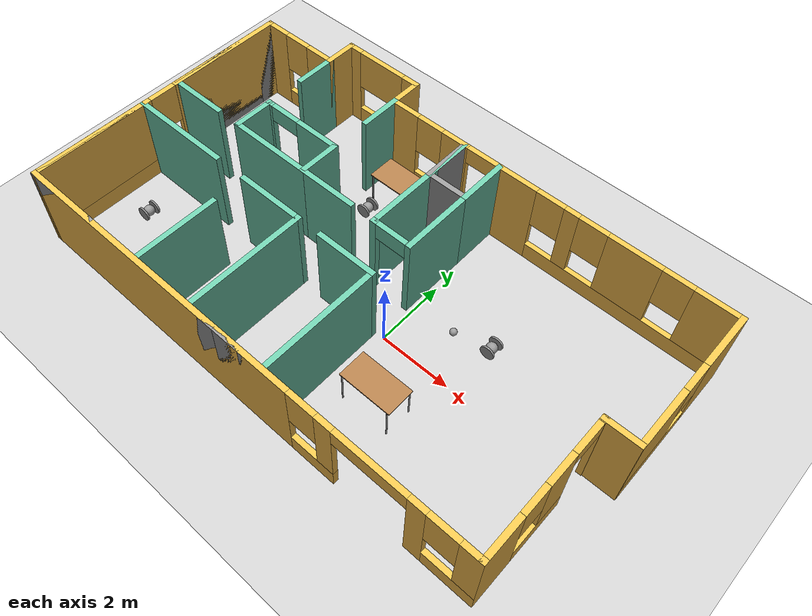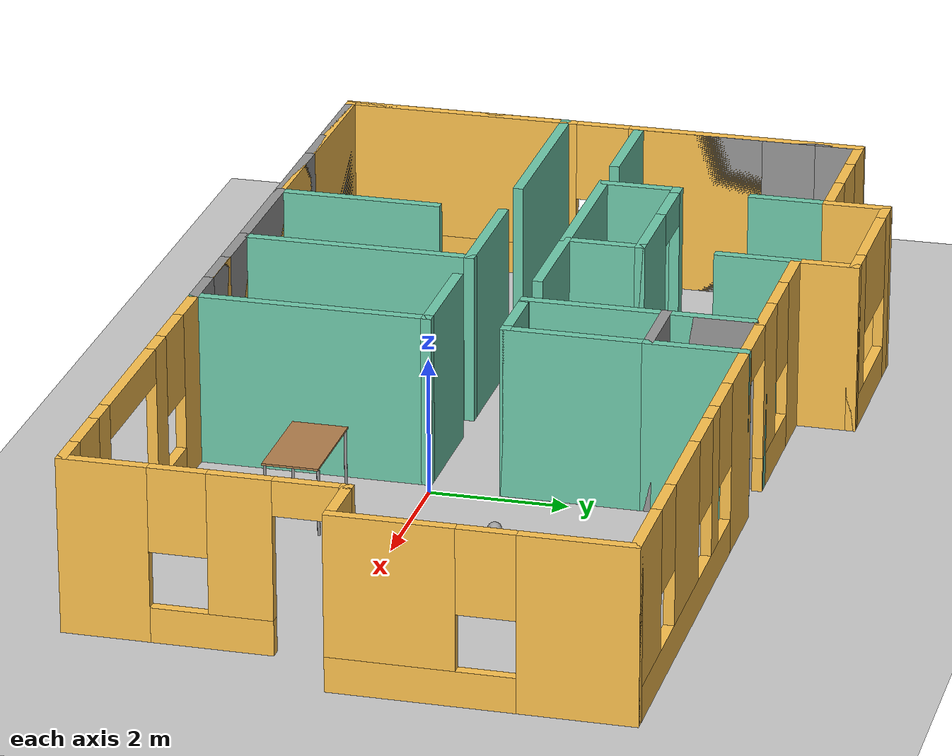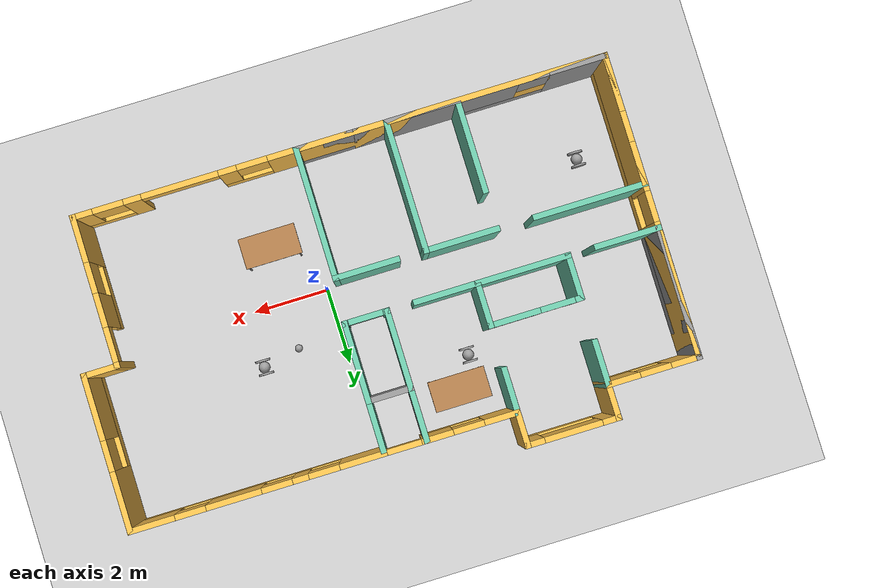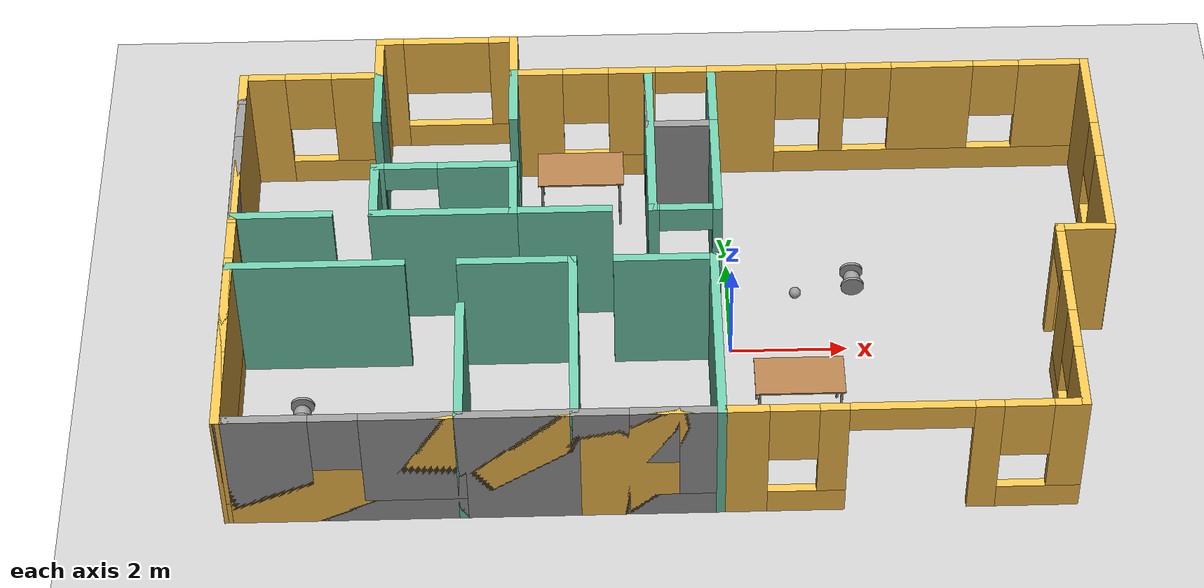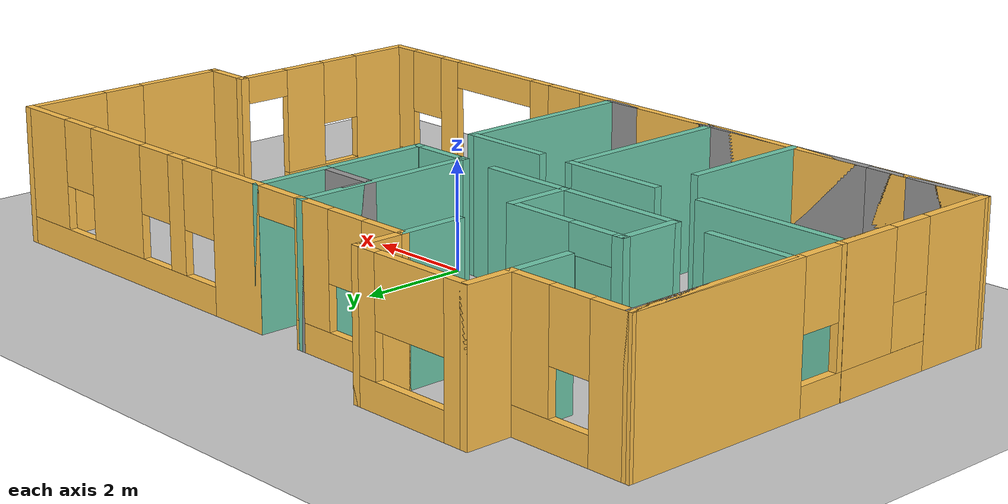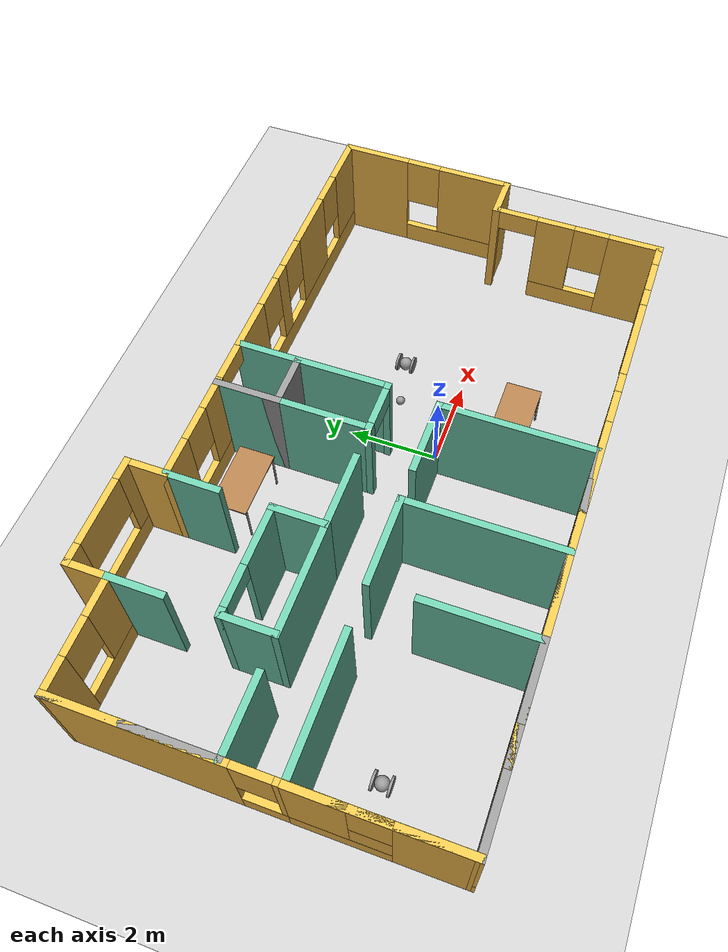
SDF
<sdf version="1.7">
 <world name="default">
  <plugin name="hello" filename="libhello.so"/>
  <light name="sun" type="directional">
   <pose>0 0 10 0 -0 0</pose>
   <diffuse>0.8 0.8 0.8 1</diffuse>
   <specular>0.2 0.2 0.2 1</specular>
   <attenuation>
    <range>1000</range>
    <constant>0.9</constant>
    <linear>0.01</linear>
    <quadratic>0.001</quadratic>
   </attenuation>
   <direction>-0.5 0.1 -0.9</direction>
   <spot><inner_angle>0</inner_angle><outer_angle>0</outer_angle><falloff>0</falloff></spot>
  </light>
  <model name="ground_plane">
   <static>1</static>
   <link name="link">
    <collision name="collision">
     <geometry><plane><normal>0 0 1</normal><size>100 100</size></plane></geometry>
     <surface><friction><ode><mu>100</mu><mu2>50</mu2></ode></friction></surface>
    </collision>
    <visual name="visual">
     <cast_shadows>0</cast_shadows>
     <geometry><plane><normal>0 0 1</normal><size>100 100</size></plane></geometry>
     <material>
      <script><uri>file://media/materials/scripts/gazebo.material</uri><name>Gazebo/Grey</name></script>
     </material>
    </visual>
   </link>
  </model>
  <gravity>0 0 -9.8</gravity>
  <magnetic_field>6e-06 2.3e-05 -4.2e-05</magnetic_field>
  <atmosphere type="adiabatic"/>
  <physics type="ode">
   <max_step_size>0.001</max_step_size>
   <real_time_factor>1</real_time_factor>
   <real_time_update_rate>1000</real_time_update_rate>
  </physics>
  <scene><ambient>0.4 0.4 0.4 1</ambient><background>0.7 0.7 0.7 1</background><shadows>1</shadows></scene>
  <spherical_coordinates>
   <surface_model>EARTH_WGS84</surface_model>
   <latitude_deg>0</latitude_deg>
   <longitude_deg>0</longitude_deg>
   <elevation>0</elevation>
   <heading_deg>0</heading_deg>
  </spherical_coordinates>
  <model name="house">
   <pose>-1.00559 0.90173 0 0 -0 0</pose>
   <link name="Wall_0">
    <pose>-6.16995 3.50005 0 0 -0 0</pose>
    <visual name="Wall_0_Visual_0">
     <pose>-0.852569 0 1.25 0 -0 0</pose>
     <geometry><box><size>0.794862 0.15 2.5</size></box></geometry>
     <material>
      <script><uri>file://media/materials/scripts/gazebo.material</uri><name>Gazebo/Grey</name></script>
      <ambient>1 0.764706 0.305882 1</ambient>
     </material>
     <meta><layer>0</layer></meta>
    </visual>
    <collision name="Wall_0_Collision_0">
     <geometry><box><size>0.794862 0.15 2.5</size></box></geometry>
     <pose>-0.852569 0 1.25 0 -0 0</pose>
    </collision>
    <visual name="Wall_0_Visual_1">
     <pose>0.397431 0 0.25 0 -0 0</pose>
     <geometry><box><size>1.70514 0.15 0.5</size></box></geometry>
     <material>
      <script><uri>file://media/materials/scripts/gazebo.material</uri><name>Gazebo/Grey</name></script>
      <ambient>1 0.764706 0.305882 1</ambient>
     </material>
     <meta><layer>0</layer></meta>
    </visual>
    <collision name="Wall_0_Collision_1">
     <geometry><box><size>1.70514 0.15 0.5</size></box></geometry>
     <pose>0.397431 0 0.25 0 -0 0</pose>
    </collision>
    <visual name="Wall_0_Visual_2">
     <pose>0.797431 0 1.5 0 -0 0</pose>
     <geometry><box><size>0.905138 0.15 2</size></box></geometry>
     <material>
      <script><uri>file://media/materials/scripts/gazebo.material</uri><name>Gazebo/Grey</name></script>
      <ambient>1 0.764706 0.305882 1</ambient>
     </material>
     <meta><layer>0</layer></meta>
    </visual>
    <collision name="Wall_0_Collision_2">
     <geometry><box><size>0.905138 0.15 2</size></box></geometry>
     <pose>0.797431 0 1.5 0 -0 0</pose>
    </collision>
    <visual name="Wall_0_Visual_3">
     <pose>-0.055138 0 1.9 0 -0 0</pose>
     <geometry><box><size>0.8 0.15 1.2</size></box></geometry>
     <material>
      <script><uri>file://media/materials/scripts/gazebo.material</uri><name>Gazebo/Grey</name></script>
      <ambient>1 0.764706 0.305882 1</ambient>
     </material>
     <meta><layer>0</layer></meta>
    </visual>
    <collision name="Wall_0_Collision_3">
     <geometry><box><size>0.8 0.15 1.2</size></box></geometry>
     <pose>-0.055138 0 1.9 0 -0 0</pose>
    </collision>
   </link>
   <link name="Wall_1">
    <collision name="Wall_1_Collision">
     <geometry><box><size>1 0.15 2.5</size></box></geometry>
     <pose>0 0 1.25 0 -0 0</pose>
    </collision>
    <visual name="Wall_1_Visual">
     <pose>0 0 1.25 0 -0 0</pose>
     <geometry><box><size>1 0.15 2.5</size></box></geometry>
     <material>
      <script><uri>file://media/materials/scripts/gazebo.material</uri><name>Gazebo/Grey</name></script>
      <ambient>1 0.764706 0.305882 1</ambient>
     </material>
     <meta><layer>0</layer></meta>
    </visual>
    <pose>-4.99495 3.92505 0 0 -0 1.5708</pose>
   </link>
   <link name="Wall_10">
    <pose>6.49505 -2.42495 0 0 -0 1.5708</pose>
    <visual name="Wall_10_Visual_0">
     <pose>-1.37895 0 1.25 0 -0 0</pose>
     <geometry><box><size>1.24209 0.15 2.5</size></box></geometry>
     <material>
      <script><uri>file://media/materials/scripts/gazebo.material</uri><name>Gazebo/Grey</name></script>
      <ambient>1 0.764706 0.305882 1</ambient>
     </material>
     <meta><layer>0</layer></meta>
    </visual>
    <collision name="Wall_10_Collision_0">
     <geometry><box><size>1.24209 0.15 2.5</size></box></geometry>
     <pose>-1.37895 0 1.25 0 -0 0</pose>
    </collision>
    <visual name="Wall_10_Visual_1">
     <pose>1.91295 0 1.25 0 -0 0</pose>
     <geometry><box><size>0.174109 0.15 2.5</size></box></geometry>
     <material>
      <script><uri>file://media/materials/scripts/gazebo.material</uri><name>Gazebo/Grey</name></script>
      <ambient>1 0.764706 0.305882 1</ambient>
     </material>
     <meta><layer>0</layer></meta>
    </visual>
    <collision name="Wall_10_Collision_1">
     <geometry><box><size>0.174109 0.15 2.5</size></box></geometry>
     <pose>1.91295 0 1.25 0 -0 0</pose>
    </collision>
    <visual name="Wall_10_Visual_2">
     <pose>0.083992 0 0.25 0 -0 0</pose>
     <geometry><box><size>1.6838 0.15 0.5</size></box></geometry>
     <material>
      <script><uri>file://media/materials/scripts/gazebo.material</uri><name>Gazebo/Grey</name></script>
      <ambient>1 0.764706 0.305882 1</ambient>
     </material>
     <meta><layer>0</layer></meta>
    </visual>
    <collision name="Wall_10_Collision_2">
     <geometry><box><size>1.6838 0.15 0.5</size></box></geometry>
     <pose>0.083992 0 0.25 0 -0 0</pose>
    </collision>
    <visual name="Wall_10_Visual_3">
     <pose>0.483992 0 1.5 0 -0 0</pose>
     <geometry><box><size>0.883798 0.15 2</size></box></geometry>
     <material>
      <script><uri>file://media/materials/scripts/gazebo.material</uri><name>Gazebo/Grey</name></script>
      <ambient>1 0.764706 0.305882 1</ambient>
     </material>
     <meta><layer>0</layer></meta>
    </visual>
    <collision name="Wall_10_Collision_3">
     <geometry><box><size>0.883798 0.15 2</size></box></geometry>
     <pose>0.483992 0 1.5 0 -0 0</pose>
    </collision>
    <visual name="Wall_10_Visual_4">
     <pose>-0.357906 0 1.9 0 -0 0</pose>
     <geometry><box><size>0.8 0.15 1.2</size></box></geometry>
     <material>
      <script><uri>file://media/materials/scripts/gazebo.material</uri><name>Gazebo/Grey</name></script>
      <ambient>1 0.764706 0.305882 1</ambient>
     </material>
     <meta><layer>0</layer></meta>
    </visual>
    <collision name="Wall_10_Collision_4">
     <geometry><box><size>0.8 0.15 1.2</size></box></geometry>
     <pose>-0.357906 0 1.9 0 -0 0</pose>
    </collision>
    <visual name="Wall_10_Visual_5">
     <pose>1.37589 0 2.25 0 -0 0</pose>
     <geometry><box><size>0.9 0.15 0.5</size></box></geometry>
     <material>
      <script><uri>file://media/materials/scripts/gazebo.material</uri><name>Gazebo/Grey</name></script>
      <ambient>1 0.764706 0.305882 1</ambient>
     </material>
     <meta><layer>0</layer></meta>
    </visual>
    <collision name="Wall_10_Collision_5">
     <geometry><box><size>0.9 0.15 0.5</size></box></geometry>
     <pose>1.37589 0 2.25 0 -0 0</pose>
    </collision>
   </link>
   <link name="Wall_12">
    <collision name="Wall_12_Collision">
     <geometry><box><size>1 0.15 2.5</size></box></geometry>
     <pose>0 0 1.25 0 -0 0</pose>
    </collision>
    <visual name="Wall_12_Visual">
     <pose>0 0 1.25 0 -0 0</pose>
     <geometry><box><size>1 0.15 2.5</size></box></geometry>
     <material>
      <script><uri>file://media/materials/scripts/gazebo.material</uri><name>Gazebo/Grey</name></script>
      <ambient>1 0.764706 0.305882 1</ambient>
     </material>
     <meta><layer>0</layer></meta>
    </visual>
    <pose>6.92005 -0.499954 0 0 -0 0</pose>
   </link>
   <link name="Wall_15">
    <pose>7.35505 1.50005 0 0 0 -1.5708</pose>
    <visual name="Wall_15_Visual_0">
     <pose>-1.2709 0 1.25 0 -0 0</pose>
     <geometry><box><size>1.6082 0.15 2.5</size></box></geometry>
     <material>
      <script><uri>file://media/materials/scripts/gazebo.material</uri><name>Gazebo/Grey</name></script>
      <ambient>1 0.764706 0.305882 1</ambient>
     </material>
     <meta><layer>0</layer></meta>
    </visual>
    <collision name="Wall_15_Collision_0">
     <geometry><box><size>1.6082 0.15 2.5</size></box></geometry>
     <pose>-1.2709 0 1.25 0 -0 0</pose>
    </collision>
    <visual name="Wall_15_Visual_1">
     <pose>0.804102 0 0.25 0 -0 0</pose>
     <geometry><box><size>2.5418 0.15 0.5</size></box></geometry>
     <material>
      <script><uri>file://media/materials/scripts/gazebo.material</uri><name>Gazebo/Grey</name></script>
      <ambient>1 0.764706 0.305882 1</ambient>
     </material>
     <meta><layer>0</layer></meta>
    </visual>
    <collision name="Wall_15_Collision_1">
     <geometry><box><size>2.5418 0.15 0.5</size></box></geometry>
     <pose>0.804102 0 0.25 0 -0 0</pose>
    </collision>
    <visual name="Wall_15_Visual_2">
     <pose>1.2041 0 1.5 0 -0 0</pose>
     <geometry><box><size>1.7418 0.15 2</size></box></geometry>
     <material>
      <script><uri>file://media/materials/scripts/gazebo.material</uri><name>Gazebo/Grey</name></script>
      <ambient>1 0.764706 0.305882 1</ambient>
     </material>
     <meta><layer>0</layer></meta>
    </visual>
    <collision name="Wall_15_Collision_2">
     <geometry><box><size>1.7418 0.15 2</size></box></geometry>
     <pose>1.2041 0 1.5 0 -0 0</pose>
    </collision>
    <visual name="Wall_15_Visual_3">
     <pose>-0.066796 0 1.9 0 -0 0</pose>
     <geometry><box><size>0.8 0.15 1.2</size></box></geometry>
     <material>
      <script><uri>file://media/materials/scripts/gazebo.material</uri><name>Gazebo/Grey</name></script>
      <ambient>1 0.764706 0.305882 1</ambient>
     </material>
     <meta><layer>0</layer></meta>
    </visual>
    <collision name="Wall_15_Collision_3">
     <geometry><box><size>0.8 0.15 1.2</size></box></geometry>
     <pose>-0.066796 0 1.9 0 -0 0</pose>
    </collision>
   </link>
   <link name="Wall_2">
    <pose>-3.81995 4.35005 0 0 -0 0</pose>
    <visual name="Wall_2_Visual_0">
     <pose>-1.0075 0 1.25 0 -0 0</pose>
     <geometry><box><size>0.485 0.15 2.5</size></box></geometry>
     <material>
      <script><uri>file://media/materials/scripts/gazebo.material</uri><name>Gazebo/Grey</name></script>
      <ambient>1 0.764706 0.305882 1</ambient>
     </material>
     <meta><layer>0</layer></meta>
    </visual>
    <collision name="Wall_2_Collision_0">
     <geometry><box><size>0.485 0.15 2.5</size></box></geometry>
     <pose>-1.0075 0 1.25 0 -0 0</pose>
    </collision>
    <visual name="Wall_2_Visual_1">
     <pose>0.2425 0 0.25 0 -0 0</pose>
     <geometry><box><size>2.015 0.15 0.5</size></box></geometry>
     <material>
      <script><uri>file://media/materials/scripts/gazebo.material</uri><name>Gazebo/Grey</name></script>
      <ambient>1 0.764706 0.305882 1</ambient>
     </material>
     <meta><layer>0</layer></meta>
    </visual>
    <collision name="Wall_2_Collision_1">
     <geometry><box><size>2.015 0.15 0.5</size></box></geometry>
     <pose>0.2425 0 0.25 0 -0 0</pose>
    </collision>
    <visual name="Wall_2_Visual_2">
     <pose>0.9925 0 1.5 0 -0 0</pose>
     <geometry><box><size>0.515 0.15 2</size></box></geometry>
     <material>
      <script><uri>file://media/materials/scripts/gazebo.material</uri><name>Gazebo/Grey</name></script>
      <ambient>1 0.764706 0.305882 1</ambient>
     </material>
     <meta><layer>0</layer></meta>
    </visual>
    <collision name="Wall_2_Collision_2">
     <geometry><box><size>0.515 0.15 2</size></box></geometry>
     <pose>0.9925 0 1.5 0 -0 0</pose>
    </collision>
    <visual name="Wall_2_Visual_3">
     <pose>-0.015 0 1.9 0 -0 0</pose>
     <geometry><box><size>1.5 0.15 1.2</size></box></geometry>
     <material>
      <script><uri>file://media/materials/scripts/gazebo.material</uri><name>Gazebo/Grey</name></script>
      <ambient>1 0.764706 0.305882 1</ambient>
     </material>
     <meta><layer>0</layer></meta>
    </visual>
    <collision name="Wall_2_Collision_3">
     <geometry><box><size>1.5 0.15 1.2</size></box></geometry>
     <pose>-0.015 0 1.9 0 -0 0</pose>
    </collision>
   </link>
   <link name="Wall_22">
    <collision name="Wall_22_Collision">
     <geometry><box><size>1.25 0.15 2.5</size></box></geometry>
     <pose>0 0 1.25 0 -0 0</pose>
    </collision>
    <visual name="Wall_22_Visual">
     <pose>0 0 1.25 0 -0 0</pose>
     <geometry><box><size>1.25 0.15 2.5</size></box></geometry>
     <material>
      <script><uri>file://media/materials/scripts/gazebo.material</uri><name>Gazebo/Grey</name></script>
      <ambient>0.435294 0.796078 0.67451 1</ambient>
     </material>
     <meta><layer>0</layer></meta>
    </visual>
    <pose>-4.99495 2.95005 0 0 0 -1.5708</pose>
   </link>
   <link name="Wall_24">
    <pose>-7.34495 1.84025 0 0 0 -1.5708</pose>
    <visual name="Wall_24_Visual_0">
     <pose>-1.36898 0 1.25 0 -0 0</pose>
     <geometry><box><size>0.731623 0.15 2.5</size></box></geometry>
     <material>
      <script><uri>file://media/materials/scripts/gazebo.material</uri><name>Gazebo/Grey</name></script>
      <ambient>1 1 1 1</ambient>
     </material>
     <meta><layer>0</layer></meta>
    </visual>
    <collision name="Wall_24_Collision_0">
     <geometry><box><size>0.731623 0.15 2.5</size></box></geometry>
     <pose>-1.36898 0 1.25 0 -0 0</pose>
    </collision>
    <visual name="Wall_24_Visual_1">
     <pose>0.365812 0 0.25 0 -0 0</pose>
     <geometry><box><size>2.73796 0.15 0.5</size></box></geometry>
     <material>
      <script><uri>file://media/materials/scripts/gazebo.material</uri><name>Gazebo/Grey</name></script>
      <ambient>1 1 1 1</ambient>
     </material>
     <meta><layer>0</layer></meta>
    </visual>
    <collision name="Wall_24_Collision_1">
     <geometry><box><size>2.73796 0.15 0.5</size></box></geometry>
     <pose>0.365812 0 0.25 0 -0 0</pose>
    </collision>
    <visual name="Wall_24_Visual_2">
     <pose>0.765812 0 1.5 0 -0 0</pose>
     <geometry><box><size>1.93796 0.15 2</size></box></geometry>
     <material>
      <script><uri>file://media/materials/scripts/gazebo.material</uri><name>Gazebo/Grey</name></script>
      <ambient>1 1 1 1</ambient>
     </material>
     <meta><layer>0</layer></meta>
    </visual>
    <collision name="Wall_24_Collision_2">
     <geometry><box><size>1.93796 0.15 2</size></box></geometry>
     <pose>0.765812 0 1.5 0 -0 0</pose>
    </collision>
    <visual name="Wall_24_Visual_3">
     <pose>-0.603168 0 1.9 0 -0 0</pose>
     <geometry><box><size>0.8 0.15 1.2</size></box></geometry>
     <material>
      <script><uri>file://media/materials/scripts/gazebo.material</uri><name>Gazebo/Grey</name></script>
      <ambient>1 1 1 1</ambient>
     </material>
     <meta><layer>0</layer></meta>
    </visual>
    <collision name="Wall_24_Collision_3">
     <geometry><box><size>0.8 0.15 1.2</size></box></geometry>
     <pose>-0.603168 0 1.9 0 -0 0</pose>
    </collision>
   </link>
   <link name="Wall_26">
    <collision name="Wall_26_Collision">
     <geometry><box><size>1.21958 0.15 2.5</size></box></geometry>
     <pose>0 0 1.25 0 -0 0</pose>
    </collision>
    <visual name="Wall_26_Visual">
     <pose>0 0 1.25 0 -0 0</pose>
     <geometry><box><size>1.21958 0.15 2.5</size></box></geometry>
     <material>
      <script><uri>file://media/materials/scripts/gazebo.material</uri><name>Gazebo/Grey</name></script>
      <ambient>0.435294 0.796078 0.67451 1</ambient>
     </material>
     <meta><layer>0</layer></meta>
    </visual>
    <pose>-4.99495 0.715255 0 0 -0 1.5708</pose>
   </link>
   <link name="Wall_29">
    <collision name="Wall_29_Collision">
     <geometry><box><size>1.25 0.15 2.5</size></box></geometry>
     <pose>0 0 1.25 0 -0 0</pose>
    </collision>
    <visual name="Wall_29_Visual">
     <pose>0 0 1.25 0 -0 0</pose>
     <geometry><box><size>1.25 0.15 2.5</size></box></geometry>
     <material>
      <script><uri>file://media/materials/scripts/gazebo.material</uri><name>Gazebo/Grey</name></script>
      <ambient>0.435294 0.796078 0.67451 1</ambient>
     </material>
     <meta><layer>0</layer></meta>
    </visual>
    <pose>-2.64495 0.700047 0 0 -0 1.5708</pose>
   </link>
   <link name="Wall_3">
    <collision name="Wall_3_Collision">
     <geometry><box><size>1 0.15 2.5</size></box></geometry>
     <pose>0 0 1.25 0 -0 0</pose>
    </collision>
    <visual name="Wall_3_Visual">
     <pose>0 0 1.25 0 -0 0</pose>
     <geometry><box><size>1 0.15 2.5</size></box></geometry>
     <material>
      <script><uri>file://media/materials/scripts/gazebo.material</uri><name>Gazebo/Grey</name></script>
      <ambient>1 0.764706 0.305882 1</ambient>
     </material>
     <meta><layer>0</layer></meta>
    </visual>
    <pose>-2.64495 3.92505 0 0 0 -1.5708</pose>
   </link>
   <link name="Wall_31">
    <collision name="Wall_31_Collision">
     <geometry><box><size>1.25 0.15 2.5</size></box></geometry>
     <pose>0 0 1.25 0 -0 0</pose>
    </collision>
    <visual name="Wall_31_Visual">
     <pose>0 0 1.25 0 -0 0</pose>
     <geometry><box><size>1.25 0.15 2.5</size></box></geometry>
     <material>
      <script><uri>file://media/materials/scripts/gazebo.material</uri><name>Gazebo/Grey</name></script>
      <ambient>0.435294 0.796078 0.67451 1</ambient>
     </material>
     <meta><layer>0</layer></meta>
    </visual>
    <pose>-2.64495 2.95005 0 0 0 -1.5708</pose>
   </link>
   <link name="Wall_34">
    <pose>-3.81995 1.25005 0 0 -0 0</pose>
    <visual name="Wall_34_Visual_0">
     <pose>-1.13392 0 1.25 0 -0 0</pose>
     <geometry><box><size>0.232165 0.15 2.5</size></box></geometry>
     <material>
      <script><uri>file://media/materials/scripts/gazebo.material</uri><name>Gazebo/Grey</name></script>
      <ambient>0.435294 0.796078 0.67451 1</ambient>
     </material>
     <meta><layer>0</layer></meta>
    </visual>
    <collision name="Wall_34_Collision_0">
     <geometry><box><size>0.232165 0.15 2.5</size></box></geometry>
     <pose>-1.13392 0 1.25 0 -0 0</pose>
    </collision>
    <visual name="Wall_34_Visual_1">
     <pose>0.566082 0 1.25 0 -0 0</pose>
     <geometry><box><size>1.36783 0.15 2.5</size></box></geometry>
     <material>
      <script><uri>file://media/materials/scripts/gazebo.material</uri><name>Gazebo/Grey</name></script>
      <ambient>0.435294 0.796078 0.67451 1</ambient>
     </material>
     <meta><layer>0</layer></meta>
    </visual>
    <collision name="Wall_34_Collision_1">
     <geometry><box><size>1.36783 0.15 2.5</size></box></geometry>
     <pose>0.566082 0 1.25 0 -0 0</pose>
    </collision>
    <visual name="Wall_34_Visual_2">
     <pose>-0.567835 0 2.25 0 -0 0</pose>
     <geometry><box><size>0.9 0.15 0.5</size></box></geometry>
     <material>
      <script><uri>file://media/materials/scripts/gazebo.material</uri><name>Gazebo/Grey</name></script>
      <ambient>0.435294 0.796078 0.67451 1</ambient>
     </material>
     <meta><layer>0</layer></meta>
    </visual>
    <collision name="Wall_34_Collision_2">
     <geometry><box><size>0.9 0.15 0.5</size></box></geometry>
     <pose>-0.567835 0 2.25 0 -0 0</pose>
    </collision>
   </link>
   <link name="Wall_37">
    <collision name="Wall_37_Collision">
     <geometry><box><size>3.5 0.15 2.5</size></box></geometry>
     <pose>0 0 1.25 0 -0 0</pose>
    </collision>
    <visual name="Wall_37_Visual">
     <pose>0 0 1.25 0 -0 0</pose>
     <geometry><box><size>3.5 0.15 2.5</size></box></geometry>
     <material>
      <script><uri>file://media/materials/scripts/gazebo.material</uri><name>Gazebo/Grey</name></script>
      <ambient>0.435294 0.796078 0.67451 1</ambient>
     </material>
     <meta><layer>0</layer></meta>
    </visual>
    <pose>-0.294953 1.82505 0 0 -0 1.5708</pose>
   </link>
   <link name="Wall_39">
    <collision name="Wall_39_Collision">
     <geometry><box><size>1.5 0.15 2.5</size></box></geometry>
     <pose>0 0 1.25 0 -0 0</pose>
    </collision>
    <visual name="Wall_39_Visual">
     <pose>0 0 1.25 0 -0 0</pose>
     <geometry><box><size>1.5 0.15 2.5</size></box></geometry>
     <material>
      <script><uri>file://media/materials/scripts/gazebo.material</uri><name>Gazebo/Grey</name></script>
      <ambient>1 1 1 1</ambient>
     </material>
     <meta><layer>0</layer></meta>
    </visual>
    <pose>-0.294953 2.82505 0 0 0 -1.5708</pose>
   </link>
   <link name="Wall_4">
    <pose>2.35505 3.50005 0 0 -0 0</pose>
    <visual name="Wall_4_Visual_0">
     <pose>-4.60938 0 1.25 0 -0 0</pose>
     <geometry><box><size>0.931245 0.15 2.5</size></box></geometry>
     <material>
      <script><uri>file://media/materials/scripts/gazebo.material</uri><name>Gazebo/Grey</name></script>
      <ambient>1 0.764706 0.305882 1</ambient>
     </material>
     <meta><layer>0</layer></meta>
    </visual>
    <collision name="Wall_4_Collision_0">
     <geometry><box><size>0.931245 0.15 2.5</size></box></geometry>
     <pose>-4.60938 0 1.25 0 -0 0</pose>
    </collision>
    <visual name="Wall_4_Visual_1">
     <pose>-1.0127 0 1.25 0 -0 0</pose>
     <geometry><box><size>1.22059 0.15 2.5</size></box></geometry>
     <material>
      <script><uri>file://media/materials/scripts/gazebo.material</uri><name>Gazebo/Grey</name></script>
      <ambient>1 0.764706 0.305882 1</ambient>
     </material>
     <meta><layer>0</layer></meta>
    </visual>
    <collision name="Wall_4_Collision_1">
     <geometry><box><size>1.22059 0.15 2.5</size></box></geometry>
     <pose>-1.0127 0 1.25 0 -0 0</pose>
    </collision>
    <visual name="Wall_4_Visual_2">
     <pose>-3.33337 0 0.25 0 -0 0</pose>
     <geometry><box><size>1.62077 0.15 0.5</size></box></geometry>
     <material>
      <script><uri>file://media/materials/scripts/gazebo.material</uri><name>Gazebo/Grey</name></script>
      <ambient>1 0.764706 0.305882 1</ambient>
     </material>
     <meta><layer>0</layer></meta>
    </visual>
    <collision name="Wall_4_Collision_2">
     <geometry><box><size>1.62077 0.15 0.5</size></box></geometry>
     <pose>-3.33337 0 0.25 0 -0 0</pose>
    </collision>
    <visual name="Wall_4_Visual_3">
     <pose>2.3363 0 0.25 0 -0 0</pose>
     <geometry><box><size>5.4774 0.15 0.5</size></box></geometry>
     <material>
      <script><uri>file://media/materials/scripts/gazebo.material</uri><name>Gazebo/Grey</name></script>
      <ambient>1 0.764706 0.305882 1</ambient>
     </material>
     <meta><layer>0</layer></meta>
    </visual>
    <collision name="Wall_4_Collision_3">
     <geometry><box><size>5.4774 0.15 0.5</size></box></geometry>
     <pose>2.3363 0 0.25 0 -0 0</pose>
    </collision>
    <visual name="Wall_4_Visual_4">
     <pose>-2.93337 0 1.5 0 -0 0</pose>
     <geometry><box><size>0.820767 0.15 2</size></box></geometry>
     <material>
      <script><uri>file://media/materials/scripts/gazebo.material</uri><name>Gazebo/Grey</name></script>
      <ambient>1 0.764706 0.305882 1</ambient>
     </material>
     <meta><layer>0</layer></meta>
    </visual>
    <collision name="Wall_4_Collision_4">
     <geometry><box><size>0.820767 0.15 2</size></box></geometry>
     <pose>-2.93337 0 1.5 0 -0 0</pose>
    </collision>
    <visual name="Wall_4_Visual_5">
     <pose>-2.93337 0 1.5 0 -0 0</pose>
     <geometry><box><size>0.820767 0.15 2</size></box></geometry>
     <material>
      <script><uri>file://media/materials/scripts/gazebo.material</uri><name>Gazebo/Grey</name></script>
      <ambient>1 0.764706 0.305882 1</ambient>
     </material>
     <meta><layer>0</layer></meta>
    </visual>
    <collision name="Wall_4_Collision_5">
     <geometry><box><size>0.820767 0.15 2</size></box></geometry>
     <pose>-2.93337 0 1.5 0 -0 0</pose>
    </collision>
    <visual name="Wall_4_Visual_6">
     <pose>0.605947 0 1.5 0 -0 0</pose>
     <geometry><box><size>0.4167 0.15 2</size></box></geometry>
     <material>
      <script><uri>file://media/materials/scripts/gazebo.material</uri><name>Gazebo/Grey</name></script>
      <ambient>1 0.764706 0.305882 1</ambient>
     </material>
     <meta><layer>0</layer></meta>
    </visual>
    <collision name="Wall_4_Collision_6">
     <geometry><box><size>0.4167 0.15 2</size></box></geometry>
     <pose>0.605947 0 1.5 0 -0 0</pose>
    </collision>
    <visual name="Wall_4_Visual_7">
     <pose>2.33214 0 1.5 0 -0 0</pose>
     <geometry><box><size>1.43569 0.15 2</size></box></geometry>
     <material>
      <script><uri>file://media/materials/scripts/gazebo.material</uri><name>Gazebo/Grey</name></script>
      <ambient>1 0.764706 0.305882 1</ambient>
     </material>
     <meta><layer>0</layer></meta>
    </visual>
    <collision name="Wall_4_Collision_7">
     <geometry><box><size>1.43569 0.15 2</size></box></geometry>
     <pose>2.33214 0 1.5 0 -0 0</pose>
    </collision>
    <visual name="Wall_4_Visual_8">
     <pose>4.46249 0 1.5 0 -0 0</pose>
     <geometry><box><size>1.22502 0.15 2</size></box></geometry>
     <material>
      <script><uri>file://media/materials/scripts/gazebo.material</uri><name>Gazebo/Grey</name></script>
      <ambient>1 0.764706 0.305882 1</ambient>
     </material>
     <meta><layer>0</layer></meta>
    </visual>
    <collision name="Wall_4_Collision_8">
     <geometry><box><size>1.22502 0.15 2</size></box></geometry>
     <pose>4.46249 0 1.5 0 -0 0</pose>
    </collision>
    <visual name="Wall_4_Visual_9">
     <pose>-3.74376 0 1.9 0 -0 0</pose>
     <geometry><box><size>0.8 0.15 1.2</size></box></geometry>
     <material>
      <script><uri>file://media/materials/scripts/gazebo.material</uri><name>Gazebo/Grey</name></script>
      <ambient>1 0.764706 0.305882 1</ambient>
     </material>
     <meta><layer>0</layer></meta>
    </visual>
    <collision name="Wall_4_Collision_9">
     <geometry><box><size>0.8 0.15 1.2</size></box></geometry>
     <pose>-3.74376 0 1.9 0 -0 0</pose>
    </collision>
    <visual name="Wall_4_Visual_10">
     <pose>-0.002403 0 1.9 0 -0 0</pose>
     <geometry><box><size>0.8 0.15 1.2</size></box></geometry>
     <material>
      <script><uri>file://media/materials/scripts/gazebo.material</uri><name>Gazebo/Grey</name></script>
      <ambient>1 0.764706 0.305882 1</ambient>
     </material>
     <meta><layer>0</layer></meta>
    </visual>
    <collision name="Wall_4_Collision_10">
     <geometry><box><size>0.8 0.15 1.2</size></box></geometry>
     <pose>-0.002403 0 1.9 0 -0 0</pose>
    </collision>
    <visual name="Wall_4_Visual_11">
     <pose>1.2143 0 1.9 0 -0 0</pose>
     <geometry><box><size>0.8 0.15 1.2</size></box></geometry>
     <material>
      <script><uri>file://media/materials/scripts/gazebo.material</uri><name>Gazebo/Grey</name></script>
      <ambient>1 0.764706 0.305882 1</ambient>
     </material>
     <meta><layer>0</layer></meta>
    </visual>
    <collision name="Wall_4_Collision_11">
     <geometry><box><size>0.8 0.15 1.2</size></box></geometry>
     <pose>1.2143 0 1.9 0 -0 0</pose>
    </collision>
    <visual name="Wall_4_Visual_12">
     <pose>3.44998 0 1.9 0 -0 0</pose>
     <geometry><box><size>0.8 0.15 1.2</size></box></geometry>
     <material>
      <script><uri>file://media/materials/scripts/gazebo.material</uri><name>Gazebo/Grey</name></script>
      <ambient>1 0.764706 0.305882 1</ambient>
     </material>
     <meta><layer>0</layer></meta>
    </visual>
    <collision name="Wall_4_Collision_12">
     <geometry><box><size>0.8 0.15 1.2</size></box></geometry>
     <pose>3.44998 0 1.9 0 -0 0</pose>
    </collision>
    <visual name="Wall_4_Visual_13">
     <pose>-2.07299 0 2.25 0 -0 0</pose>
     <geometry><box><size>0.9 0.15 0.5</size></box></geometry>
     <material>
      <script><uri>file://media/materials/scripts/gazebo.material</uri><name>Gazebo/Grey</name></script>
      <ambient>1 0.764706 0.305882 1</ambient>
     </material>
     <meta><layer>0</layer></meta>
    </visual>
    <collision name="Wall_4_Collision_13">
     <geometry><box><size>0.9 0.15 0.5</size></box></geometry>
     <pose>-2.07299 0 2.25 0 -0 0</pose>
    </collision>
    <visual name="Wall_4_Visual_14">
     <pose>-2.07299 0 2.25 0 -0 0</pose>
     <geometry><box><size>0.9 0.15 0.5</size></box></geometry>
     <material>
      <script><uri>file://media/materials/scripts/gazebo.material</uri><name>Gazebo/Grey</name></script>
      <ambient>1 0.764706 0.305882 1</ambient>
     </material>
     <meta><layer>0</layer></meta>
    </visual>
    <collision name="Wall_4_Collision_14">
     <geometry><box><size>0.9 0.15 0.5</size></box></geometry>
     <pose>-2.07299 0 2.25 0 -0 0</pose>
    </collision>
   </link>
   <link name="Wall_40">
    <collision name="Wall_40_Collision">
     <geometry><box><size>1.25 0.15 2.5</size></box></geometry>
     <pose>0 0 1.25 0 -0 0</pose>
    </collision>
    <visual name="Wall_40_Visual">
     <pose>0 0 1.25 0 -0 0</pose>
     <geometry><box><size>1.25 0.15 2.5</size></box></geometry>
     <material>
      <script><uri>file://media/materials/scripts/gazebo.material</uri><name>Gazebo/Grey</name></script>
      <ambient>1 1 1 1</ambient>
     </material>
     <meta><layer>0</layer></meta>
    </visual>
    <pose>0.255048 2.15005 0 0 -0 0</pose>
   </link>
   <link name="Wall_41">
    <collision name="Wall_41_Collision">
     <geometry><box><size>1.5 0.15 2.5</size></box></geometry>
     <pose>0 0 1.25 0 -0 0</pose>
    </collision>
    <visual name="Wall_41_Visual">
     <pose>0 0 1.25 0 -0 0</pose>
     <geometry><box><size>1.5 0.15 2.5</size></box></geometry>
     <material>
      <script><uri>file://media/materials/scripts/gazebo.material</uri><name>Gazebo/Grey</name></script>
      <ambient>0.435294 0.796078 0.67451 1</ambient>
     </material>
     <meta><layer>0</layer></meta>
    </visual>
    <pose>0.805048 2.82505 0 0 -0 1.5708</pose>
   </link>
   <link name="Wall_43">
    <pose>0.255048 0.150046 0 0 -0 0</pose>
    <visual name="Wall_43_Visual_0">
     <pose>-0.532739 0 1.25 0 -0 0</pose>
     <geometry><box><size>0.184521 0.15 2.5</size></box></geometry>
     <material>
      <script><uri>file://media/materials/scripts/gazebo.material</uri><name>Gazebo/Grey</name></script>
      <ambient>0.435294 0.796078 0.67451 1</ambient>
     </material>
     <meta><layer>0</layer></meta>
    </visual>
    <collision name="Wall_43_Collision_0">
     <geometry><box><size>0.184521 0.15 2.5</size></box></geometry>
     <pose>-0.532739 0 1.25 0 -0 0</pose>
    </collision>
    <visual name="Wall_43_Visual_1">
     <pose>0.542261 0 1.25 0 -0 0</pose>
     <geometry><box><size>0.165479 0.15 2.5</size></box></geometry>
     <material>
      <script><uri>file://media/materials/scripts/gazebo.material</uri><name>Gazebo/Grey</name></script>
      <ambient>0.435294 0.796078 0.67451 1</ambient>
     </material>
     <meta><layer>0</layer></meta>
    </visual>
    <collision name="Wall_43_Collision_1">
     <geometry><box><size>0.165479 0.15 2.5</size></box></geometry>
     <pose>0.542261 0 1.25 0 -0 0</pose>
    </collision>
    <visual name="Wall_43_Visual_2">
     <pose>0.009521 0 2.25 0 -0 0</pose>
     <geometry><box><size>0.9 0.15 0.5</size></box></geometry>
     <material>
      <script><uri>file://media/materials/scripts/gazebo.material</uri><name>Gazebo/Grey</name></script>
      <ambient>0.435294 0.796078 0.67451 1</ambient>
     </material>
     <meta><layer>0</layer></meta>
    </visual>
    <collision name="Wall_43_Collision_2">
     <geometry><box><size>0.9 0.15 0.5</size></box></geometry>
     <pose>0.009521 0 2.25 0 -0 0</pose>
    </collision>
   </link>
   <link name="Wall_44">
    <collision name="Wall_44_Collision">
     <geometry><box><size>2.15 0.15 2.5</size></box></geometry>
     <pose>0 0 1.25 0 -0 0</pose>
    </collision>
    <visual name="Wall_44_Visual">
     <pose>0 0 1.25 0 -0 0</pose>
     <geometry><box><size>2.15 0.15 2.5</size></box></geometry>
     <material>
      <script><uri>file://media/materials/scripts/gazebo.material</uri><name>Gazebo/Grey</name></script>
      <ambient>0.435294 0.796078 0.67451 1</ambient>
     </material>
     <meta><layer>0</layer></meta>
    </visual>
    <pose>0.805048 1.15005 0 0 -0 1.5708</pose>
   </link>
   <link name="Wall_46">
    <pose>-7.35495 -2.67495 0 0 -0 1.5708</pose>
    <visual name="Wall_46_Visual_0">
     <pose>-0.98447 0 1.25 0 -0 0</pose>
     <geometry><box><size>1.53106 0.15 2.5</size></box></geometry>
     <material>
      <script><uri>file://media/materials/scripts/gazebo.material</uri><name>Gazebo/Grey</name></script>
      <ambient>1 0.764706 0.305882 1</ambient>
     </material>
     <meta><layer>0</layer></meta>
    </visual>
    <collision name="Wall_46_Collision_0">
     <geometry><box><size>1.53106 0.15 2.5</size></box></geometry>
     <pose>-0.98447 0 1.25 0 -0 0</pose>
    </collision>
    <visual name="Wall_46_Visual_1">
     <pose>0.76553 0 0.25 0 -0 0</pose>
     <geometry><box><size>1.96894 0.15 0.5</size></box></geometry>
     <material>
      <script><uri>file://media/materials/scripts/gazebo.material</uri><name>Gazebo/Grey</name></script>
      <ambient>1 0.764706 0.305882 1</ambient>
     </material>
     <meta><layer>0</layer></meta>
    </visual>
    <collision name="Wall_46_Collision_1">
     <geometry><box><size>1.96894 0.15 0.5</size></box></geometry>
     <pose>0.76553 0 0.25 0 -0 0</pose>
    </collision>
    <visual name="Wall_46_Visual_2">
     <pose>1.16553 0 1.5 0 -0 0</pose>
     <geometry><box><size>1.16894 0.15 2</size></box></geometry>
     <material>
      <script><uri>file://media/materials/scripts/gazebo.material</uri><name>Gazebo/Grey</name></script>
      <ambient>1 0.764706 0.305882 1</ambient>
     </material>
     <meta><layer>0</layer></meta>
    </visual>
    <collision name="Wall_46_Collision_2">
     <geometry><box><size>1.16894 0.15 2</size></box></geometry>
     <pose>1.16553 0 1.5 0 -0 0</pose>
    </collision>
    <visual name="Wall_46_Visual_3">
     <pose>0.18106 0 1.9 0 -0 0</pose>
     <geometry><box><size>0.8 0.15 1.2</size></box></geometry>
     <material>
      <script><uri>file://media/materials/scripts/gazebo.material</uri><name>Gazebo/Grey</name></script>
      <ambient>1 0.764706 0.305882 1</ambient>
     </material>
     <meta><layer>0</layer></meta>
    </visual>
    <collision name="Wall_46_Collision_3">
     <geometry><box><size>0.8 0.15 1.2</size></box></geometry>
     <pose>0.18106 0 1.9 0 -0 0</pose>
    </collision>
   </link>
   <link name="Wall_47">
    <collision name="Wall_47_Collision">
     <geometry><box><size>3 0.15 2.5</size></box></geometry>
     <pose>0 0 1.25 0 -0 0</pose>
    </collision>
    <visual name="Wall_47_Visual">
     <pose>0 0 1.25 0 -0 0</pose>
     <geometry><box><size>3 0.15 2.5</size></box></geometry>
     <material>
      <script><uri>file://media/materials/scripts/gazebo.material</uri><name>Gazebo/Grey</name></script>
      <ambient>0.435294 0.796078 0.67451 1</ambient>
     </material>
     <meta><layer>0</layer></meta>
    </visual>
    <pose>-5.92995 -0.999954 0 0 -0 0</pose>
   </link>
   <link name="Wall_50">
    <pose>-5.42995 -4.34995 0 0 -0 0</pose>
    <visual name="Wall_50_Visual_0">
     <pose>-1.23256 0 1.25 0 -0 0</pose>
     <geometry><box><size>1.53488 0.15 2.5</size></box></geometry>
     <material>
      <script><uri>file://media/materials/scripts/gazebo.material</uri><name>Gazebo/Grey</name></script>
      <ambient>1 1 1 1</ambient>
     </material>
     <meta><layer>0</layer></meta>
    </visual>
    <collision name="Wall_50_Collision_0">
     <geometry><box><size>1.53488 0.15 2.5</size></box></geometry>
     <pose>-1.23256 0 1.25 0 -0 0</pose>
    </collision>
    <visual name="Wall_50_Visual_1">
     <pose>0.767441 0 0.25 0 -0 0</pose>
     <geometry><box><size>2.46512 0.15 0.5</size></box></geometry>
     <material>
      <script><uri>file://media/materials/scripts/gazebo.material</uri><name>Gazebo/Grey</name></script>
      <ambient>1 1 1 1</ambient>
     </material>
     <meta><layer>0</layer></meta>
    </visual>
    <collision name="Wall_50_Collision_1">
     <geometry><box><size>2.46512 0.15 0.5</size></box></geometry>
     <pose>0.767441 0 0.25 0 -0 0</pose>
    </collision>
    <visual name="Wall_50_Visual_2">
     <pose>1.16744 0 1.5 0 -0 0</pose>
     <geometry><box><size>1.66512 0.15 2</size></box></geometry>
     <material>
      <script><uri>file://media/materials/scripts/gazebo.material</uri><name>Gazebo/Grey</name></script>
      <ambient>1 1 1 1</ambient>
     </material>
     <meta><layer>0</layer></meta>
    </visual>
    <collision name="Wall_50_Collision_2">
     <geometry><box><size>1.66512 0.15 2</size></box></geometry>
     <pose>1.16744 0 1.5 0 -0 0</pose>
    </collision>
    <visual name="Wall_50_Visual_3">
     <pose>-0.065117 0 1.9 0 -0 0</pose>
     <geometry><box><size>0.8 0.15 1.2</size></box></geometry>
     <material>
      <script><uri>file://media/materials/scripts/gazebo.material</uri><name>Gazebo/Grey</name></script>
      <ambient>1 1 1 1</ambient>
     </material>
     <meta><layer>0</layer></meta>
    </visual>
    <collision name="Wall_50_Collision_3">
     <geometry><box><size>0.8 0.15 1.2</size></box></geometry>
     <pose>-0.065117 0 1.9 0 -0 0</pose>
    </collision>
   </link>
   <link name="Wall_53">
    <collision name="Wall_53_Collision">
     <geometry><box><size>2 0.15 2.5</size></box></geometry>
     <pose>0 0 1.25 0 -0 0</pose>
    </collision>
    <visual name="Wall_53_Visual">
     <pose>0 0 1.25 0 -0 0</pose>
     <geometry><box><size>2 0.15 2.5</size></box></geometry>
     <material>
      <script><uri>file://media/materials/scripts/gazebo.material</uri><name>Gazebo/Grey</name></script>
      <ambient>1 1 1 1</ambient>
     </material>
     <meta><layer>0</layer></meta>
    </visual>
    <pose>-2.57995 -4.34995 0 0 -0 0</pose>
   </link>
   <link name="Wall_54">
    <collision name="Wall_54_Collision">
     <geometry><box><size>3.5 0.15 2.5</size></box></geometry>
     <pose>0 0 1.25 0 -0 0</pose>
    </collision>
    <visual name="Wall_54_Visual">
     <pose>0 0 1.25 0 -0 0</pose>
     <geometry><box><size>3.5 0.15 2.5</size></box></geometry>
     <material>
      <script><uri>file://media/materials/scripts/gazebo.material</uri><name>Gazebo/Grey</name></script>
      <ambient>0.435294 0.796078 0.67451 1</ambient>
     </material>
     <meta><layer>0</layer></meta>
    </visual>
    <pose>-1.65495 -2.67495 0 0 -0 1.5708</pose>
   </link>
   <link name="Wall_56">
    <collision name="Wall_56_Collision">
     <geometry><box><size>2 0.15 2.5</size></box></geometry>
     <pose>0 0 1.25 0 -0 0</pose>
    </collision>
    <visual name="Wall_56_Visual">
     <pose>0 0 1.25 0 -0 0</pose>
     <geometry><box><size>2 0.15 2.5</size></box></geometry>
     <material>
      <script><uri>file://media/materials/scripts/gazebo.material</uri><name>Gazebo/Grey</name></script>
      <ambient>0.435294 0.796078 0.67451 1</ambient>
     </material>
     <meta><layer>0</layer></meta>
    </visual>
    <pose>-2.57995 -0.999954 0 0 -0 0</pose>
   </link>
   <link name="Wall_59">
    <collision name="Wall_59_Collision">
     <geometry><box><size>2.5 0.15 2.5</size></box></geometry>
     <pose>0 0 1.25 0 -0 0</pose>
    </collision>
    <visual name="Wall_59_Visual">
     <pose>0 0 1.25 0 -0 0</pose>
     <geometry><box><size>2.5 0.15 2.5</size></box></geometry>
     <material>
      <script><uri>file://media/materials/scripts/gazebo.material</uri><name>Gazebo/Grey</name></script>
      <ambient>0.435294 0.796078 0.67451 1</ambient>
     </material>
     <meta><layer>0</layer></meta>
    </visual>
    <pose>-3.50495 -3.17495 0 0 -0 1.5708</pose>
   </link>
   <link name="Wall_6">
    <pose>-7.34995 -0.424953 0 0 0 -1.57207</pose>
    <visual name="Wall_6_Visual_0">
     <pose>-2.20732 0 1.25 0 -0 0</pose>
     <geometry><box><size>3.58536 0.15 2.5</size></box></geometry>
     <material>
      <script><uri>file://media/materials/scripts/gazebo.material</uri><name>Gazebo/Grey</name></script>
      <ambient>1 0.764706 0.305882 1</ambient>
     </material>
     <meta><layer>0</layer></meta>
    </visual>
    <collision name="Wall_6_Collision_0">
     <geometry><box><size>3.58536 0.15 2.5</size></box></geometry>
     <pose>-2.20732 0 1.25 0 -0 0</pose>
    </collision>
    <visual name="Wall_6_Visual_1">
     <pose>1.79268 0 0.25 0 -0 0</pose>
     <geometry><box><size>4.41464 0.15 0.5</size></box></geometry>
     <material>
      <script><uri>file://media/materials/scripts/gazebo.material</uri><name>Gazebo/Grey</name></script>
      <ambient>1 0.764706 0.305882 1</ambient>
     </material>
     <meta><layer>0</layer></meta>
    </visual>
    <collision name="Wall_6_Collision_1">
     <geometry><box><size>4.41464 0.15 0.5</size></box></geometry>
     <pose>1.79268 0 0.25 0 -0 0</pose>
    </collision>
    <visual name="Wall_6_Visual_2">
     <pose>2.19268 0 1.5 0 -0 0</pose>
     <geometry><box><size>3.61464 0.15 2</size></box></geometry>
     <material>
      <script><uri>file://media/materials/scripts/gazebo.material</uri><name>Gazebo/Grey</name></script>
      <ambient>1 0.764706 0.305882 1</ambient>
     </material>
     <meta><layer>0</layer></meta>
    </visual>
    <collision name="Wall_6_Collision_2">
     <geometry><box><size>3.61464 0.15 2</size></box></geometry>
     <pose>2.19268 0 1.5 0 -0 0</pose>
    </collision>
    <visual name="Wall_6_Visual_3">
     <pose>-0.014638 0 1.9 0 -0 0</pose>
     <geometry><box><size>0.8 0.15 1.2</size></box></geometry>
     <material>
      <script><uri>file://media/materials/scripts/gazebo.material</uri><name>Gazebo/Grey</name></script>
      <ambient>1 0.764706 0.305882 1</ambient>
     </material>
     <meta><layer>0</layer></meta>
    </visual>
    <collision name="Wall_6_Collision_3">
     <geometry><box><size>0.8 0.15 1.2</size></box></geometry>
     <pose>-0.014638 0 1.9 0 -0 0</pose>
    </collision>
   </link>
   <link name="Wall_61">
    <pose>-0.479952 -4.34995 0 0 -0 0</pose>
    <visual name="Wall_61_Visual_0">
     <pose>-0.777489 0 1.25 0 -0 0</pose>
     <geometry><box><size>0.945023 0.15 2.5</size></box></geometry>
     <material>
      <script><uri>file://media/materials/scripts/gazebo.material</uri><name>Gazebo/Grey</name></script>
      <ambient>1 1 1 1</ambient>
     </material>
     <meta><layer>0</layer></meta>
    </visual>
    <collision name="Wall_61_Collision_0">
     <geometry><box><size>0.945023 0.15 2.5</size></box></geometry>
     <pose>-0.777489 0 1.25 0 -0 0</pose>
    </collision>
    <visual name="Wall_61_Visual_1">
     <pose>0.472511 0 0.25 0 -0 0</pose>
     <geometry><box><size>1.55498 0.15 0.5</size></box></geometry>
     <material>
      <script><uri>file://media/materials/scripts/gazebo.material</uri><name>Gazebo/Grey</name></script>
      <ambient>1 1 1 1</ambient>
     </material>
     <meta><layer>0</layer></meta>
    </visual>
    <collision name="Wall_61_Collision_1">
     <geometry><box><size>1.55498 0.15 0.5</size></box></geometry>
     <pose>0.472511 0 0.25 0 -0 0</pose>
    </collision>
    <visual name="Wall_61_Visual_2">
     <pose>0.872511 0 1.5 0 -0 0</pose>
     <geometry><box><size>0.754977 0.15 2</size></box></geometry>
     <material>
      <script><uri>file://media/materials/scripts/gazebo.material</uri><name>Gazebo/Grey</name></script>
      <ambient>1 1 1 1</ambient>
     </material>
     <meta><layer>0</layer></meta>
    </visual>
    <collision name="Wall_61_Collision_2">
     <geometry><box><size>0.754977 0.15 2</size></box></geometry>
     <pose>0.872511 0 1.5 0 -0 0</pose>
    </collision>
    <visual name="Wall_61_Visual_3">
     <pose>0.095023 0 1.9 0 -0 0</pose>
     <geometry><box><size>0.8 0.15 1.2</size></box></geometry>
     <material>
      <script><uri>file://media/materials/scripts/gazebo.material</uri><name>Gazebo/Grey</name></script>
      <ambient>1 1 1 1</ambient>
     </material>
     <meta><layer>0</layer></meta>
    </visual>
    <collision name="Wall_61_Collision_3">
     <geometry><box><size>0.8 0.15 1.2</size></box></geometry>
     <pose>0.095023 0 1.9 0 -0 0</pose>
    </collision>
   </link>
   <link name="Wall_62">
    <collision name="Wall_62_Collision">
     <geometry><box><size>3.5 0.15 2.5</size></box></geometry>
     <pose>0 0 1.25 0 -0 0</pose>
    </collision>
    <visual name="Wall_62_Visual">
     <pose>0 0 1.25 0 -0 0</pose>
     <geometry><box><size>3.5 0.15 2.5</size></box></geometry>
     <material>
      <script><uri>file://media/materials/scripts/gazebo.material</uri><name>Gazebo/Grey</name></script>
      <ambient>0.435294 0.796078 0.67451 1</ambient>
     </material>
     <meta><layer>0</layer></meta>
    </visual>
    <pose>0.695048 -2.67495 0 0 -0 1.5708</pose>
   </link>
   <link name="Wall_63">
    <collision name="Wall_63_Collision">
     <geometry><box><size>1.75 0.15 2.5</size></box></geometry>
     <pose>0 0 1.25 0 -0 0</pose>
    </collision>
    <visual name="Wall_63_Visual">
     <pose>0 0 1.25 0 -0 0</pose>
     <geometry><box><size>1.75 0.15 2.5</size></box></geometry>
     <material>
      <script><uri>file://media/materials/scripts/gazebo.material</uri><name>Gazebo/Grey</name></script>
      <ambient>0.435294 0.796078 0.67451 1</ambient>
     </material>
     <meta><layer>0</layer></meta>
    </visual>
    <pose>-0.104953 -0.999954 0 0 -0 3.14159</pose>
   </link>
   <link name="Wall_65">
    <collision name="Wall_65_Collision">
     <geometry><box><size>1.75 0.15 2.5</size></box></geometry>
     <pose>0 0 1.25 0 -0 0</pose>
    </collision>
    <visual name="Wall_65_Visual">
     <pose>0 0 1.25 0 -0 0</pose>
     <geometry><box><size>1.75 0.15 2.5</size></box></geometry>
     <material>
      <script><uri>file://media/materials/scripts/gazebo.material</uri><name>Gazebo/Grey</name></script>
      <ambient>0.435294 0.796078 0.67451 1</ambient>
     </material>
     <meta><layer>0</layer></meta>
    </visual>
    <pose>-1.84495 0.150046 0 0 -0 0</pose>
   </link>
   <link name="Wall_69">
    <collision name="Wall_69_Collision">
     <geometry><box><size>3.5 0.15 2.5</size></box></geometry>
     <pose>0 0 1.25 0 -0 0</pose>
    </collision>
    <visual name="Wall_69_Visual">
     <pose>0 0 1.25 0 -0 0</pose>
     <geometry><box><size>3.5 0.15 2.5</size></box></geometry>
     <material>
      <script><uri>file://media/materials/scripts/gazebo.material</uri><name>Gazebo/Grey</name></script>
      <ambient>1 0.764706 0.305882 1</ambient>
     </material>
     <meta><layer>0</layer></meta>
    </visual>
    <pose>-7.34495 1.82505 0 0 0 -1.5708</pose>
   </link>
   <link name="Wall_70">
    <collision name="Wall_70_Collision">
     <geometry><box><size>1.75 0.15 2.5</size></box></geometry>
     <pose>0 0 1.25 0 -0 0</pose>
    </collision>
    <visual name="Wall_70_Visual">
     <pose>0 0 1.25 0 -0 0</pose>
     <geometry><box><size>1.75 0.15 2.5</size></box></geometry>
     <material>
      <script><uri>file://media/materials/scripts/gazebo.material</uri><name>Gazebo/Grey</name></script>
      <ambient>0.435294 0.796078 0.67451 1</ambient>
     </material>
     <meta><layer>0</layer></meta>
    </visual>
    <pose>-6.54495 0.150046 0 0 -0 0</pose>
   </link>
   <link name="Wall_72">
    <collision name="Wall_72_Collision">
     <geometry><box><size>2.5 0.15 2.5</size></box></geometry>
     <pose>0 0 1.25 0 -0 0</pose>
    </collision>
    <visual name="Wall_72_Visual">
     <pose>0 0 1.25 0 -0 0</pose>
     <geometry><box><size>2.5 0.15 2.5</size></box></geometry>
     <material>
      <script><uri>file://media/materials/scripts/gazebo.material</uri><name>Gazebo/Grey</name></script>
      <ambient>0.435294 0.796078 0.67451 1</ambient>
     </material>
     <meta><layer>0</layer></meta>
    </visual>
    <pose>-3.81995 0.150046 0 0 -0 3.14159</pose>
   </link>
   <link name="Wall_8">
    <pose>-0.429953 -4.34995 0 0 -0 0</pose>
    <visual name="Wall_8_Visual_0">
     <pose>-2.55965 0 1.25 0 -0 0</pose>
     <geometry><box><size>8.88071 0.15 2.5</size></box></geometry>
     <material>
      <script><uri>file://media/materials/scripts/gazebo.material</uri><name>Gazebo/Grey</name></script>
      <ambient>1 0.764706 0.305882 1</ambient>
     </material>
     <meta><layer>0</layer></meta>
    </visual>
    <collision name="Wall_8_Collision_0">
     <geometry><box><size>8.88071 0.15 2.5</size></box></geometry>
     <pose>-2.55965 0 1.25 0 -0 0</pose>
    </collision>
    <visual name="Wall_8_Visual_1">
     <pose>5.38981 0 1.25 0 -0 0</pose>
     <geometry><box><size>0.464507 0.15 2.5</size></box></geometry>
     <material>
      <script><uri>file://media/materials/scripts/gazebo.material</uri><name>Gazebo/Grey</name></script>
      <ambient>1 0.764706 0.305882 1</ambient>
     </material>
     <meta><layer>0</layer></meta>
    </visual>
    <collision name="Wall_8_Collision_1">
     <geometry><box><size>0.464507 0.15 2.5</size></box></geometry>
     <pose>5.38981 0 1.25 0 -0 0</pose>
    </collision>
    <visual name="Wall_8_Visual_2">
     <pose>2.51913 0 0.25 0 -0 0</pose>
     <geometry><box><size>1.27685 0.15 0.5</size></box></geometry>
     <material>
      <script><uri>file://media/materials/scripts/gazebo.material</uri><name>Gazebo/Grey</name></script>
      <ambient>1 0.764706 0.305882 1</ambient>
     </material>
     <meta><layer>0</layer></meta>
    </visual>
    <collision name="Wall_8_Collision_2">
     <geometry><box><size>1.27685 0.15 0.5</size></box></geometry>
     <pose>2.51913 0 0.25 0 -0 0</pose>
    </collision>
    <visual name="Wall_8_Visual_3">
     <pose>6.31103 0 0.25 0 -0 0</pose>
     <geometry><box><size>1.37794 0.15 0.5</size></box></geometry>
     <material>
      <script><uri>file://media/materials/scripts/gazebo.material</uri><name>Gazebo/Grey</name></script>
      <ambient>1 0.764706 0.305882 1</ambient>
     </material>
     <meta><layer>0</layer></meta>
    </visual>
    <collision name="Wall_8_Collision_3">
     <geometry><box><size>1.37794 0.15 0.5</size></box></geometry>
     <pose>6.31103 0 0.25 0 -0 0</pose>
    </collision>
    <visual name="Wall_8_Visual_4">
     <pose>2.91913 0 1.5 0 -0 0</pose>
     <geometry><box><size>0.476845 0.15 2</size></box></geometry>
     <material>
      <script><uri>file://media/materials/scripts/gazebo.material</uri><name>Gazebo/Grey</name></script>
      <ambient>1 0.764706 0.305882 1</ambient>
     </material>
     <meta><layer>0</layer></meta>
    </visual>
    <collision name="Wall_8_Collision_4">
     <geometry><box><size>0.476845 0.15 2</size></box></geometry>
     <pose>2.91913 0 1.5 0 -0 0</pose>
    </collision>
    <visual name="Wall_8_Visual_5">
     <pose>2.91913 0 1.5 0 -0 0</pose>
     <geometry><box><size>0.476845 0.15 2</size></box></geometry>
     <material>
      <script><uri>file://media/materials/scripts/gazebo.material</uri><name>Gazebo/Grey</name></script>
      <ambient>1 0.764706 0.305882 1</ambient>
     </material>
     <meta><layer>0</layer></meta>
    </visual>
    <collision name="Wall_8_Collision_5">
     <geometry><box><size>0.476845 0.15 2</size></box></geometry>
     <pose>2.91913 0 1.5 0 -0 0</pose>
    </collision>
    <visual name="Wall_8_Visual_6">
     <pose>6.71103 0 1.5 0 -0 0</pose>
     <geometry><box><size>0.577939 0.15 2</size></box></geometry>
     <material>
      <script><uri>file://media/materials/scripts/gazebo.material</uri><name>Gazebo/Grey</name></script>
      <ambient>1 0.764706 0.305882 1</ambient>
     </material>
     <meta><layer>0</layer></meta>
    </visual>
    <collision name="Wall_8_Collision_6">
     <geometry><box><size>0.577939 0.15 2</size></box></geometry>
     <pose>6.71103 0 1.5 0 -0 0</pose>
    </collision>
    <visual name="Wall_8_Visual_7">
     <pose>2.28071 0 1.9 0 -0 0</pose>
     <geometry><box><size>0.8 0.15 1.2</size></box></geometry>
     <material>
      <script><uri>file://media/materials/scripts/gazebo.material</uri><name>Gazebo/Grey</name></script>
      <ambient>1 0.764706 0.305882 1</ambient>
     </material>
     <meta><layer>0</layer></meta>
    </visual>
    <collision name="Wall_8_Collision_7">
     <geometry><box><size>0.8 0.15 1.2</size></box></geometry>
     <pose>2.28071 0 1.9 0 -0 0</pose>
    </collision>
    <visual name="Wall_8_Visual_8">
     <pose>6.02206 0 1.9 0 -0 0</pose>
     <geometry><box><size>0.8 0.15 1.2</size></box></geometry>
     <material>
      <script><uri>file://media/materials/scripts/gazebo.material</uri><name>Gazebo/Grey</name></script>
      <ambient>1 0.764706 0.305882 1</ambient>
     </material>
     <meta><layer>0</layer></meta>
    </visual>
    <collision name="Wall_8_Collision_8">
     <geometry><box><size>0.8 0.15 1.2</size></box></geometry>
     <pose>6.02206 0 1.9 0 -0 0</pose>
    </collision>
    <visual name="Wall_8_Visual_9">
     <pose>4.15755 0 2.25 0 -0 0</pose>
     <geometry><box><size>2 0.15 0.5</size></box></geometry>
     <material>
      <script><uri>file://media/materials/scripts/gazebo.material</uri><name>Gazebo/Grey</name></script>
      <ambient>1 0.764706 0.305882 1</ambient>
     </material>
     <meta><layer>0</layer></meta>
    </visual>
    <collision name="Wall_8_Collision_9">
     <geometry><box><size>2 0.15 0.5</size></box></geometry>
     <pose>4.15755 0 2.25 0 -0 0</pose>
    </collision>
    <visual name="Wall_8_Visual_10">
     <pose>4.15755 0 2.25 0 -0 0</pose>
     <geometry><box><size>2 0.15 0.5</size></box></geometry>
     <material>
      <script><uri>file://media/materials/scripts/gazebo.material</uri><name>Gazebo/Grey</name></script>
      <ambient>1 0.764706 0.305882 1</ambient>
     </material>
     <meta><layer>0</layer></meta>
    </visual>
    <collision name="Wall_8_Collision_10">
     <geometry><box><size>2 0.15 0.5</size></box></geometry>
     <pose>4.15755 0 2.25 0 -0 0</pose>
    </collision>
   </link>
   <static>1</static>
  </model>
  <model name="B8">
   <link name="link_4">
    <inertial>
     <mass>1</mass>
     <inertia><ixx>0.1</ixx><ixy>0</ixy><ixz>0</ixz><iyy>0.1</iyy><iyz>0</iyz><izz>0.1</izz></inertia>
    </inertial>
    <visual name="visual">
     <geometry><sphere><radius>0.15</radius></sphere></geometry>
     <material>
      <lighting>1</lighting>
      <script><uri>file://media/materials/scripts/gazebo.material</uri><name>Gazebo/Grey</name></script>
      <shader type="pixel"><normal_map>__default__</normal_map></shader>
      <ambient>0.3 0.3 0.3 1</ambient>
      <diffuse>0.7 0.7 0.7 1</diffuse>
      <specular>0.01 0.01 0.01 1</specular>
      <emissive>0 0 0 1</emissive>
     </material>
    </visual>
    <collision name="collision">
     <geometry><sphere><radius>0.15</radius></sphere></geometry>
     <surface>
      <friction>
       <ode><mu>1</mu><mu2>1</mu2><fdir1>0 0 0</fdir1><slip1>0</slip1><slip2>0</slip2></ode>
       <torsional>
        <coefficient>1</coefficient>
        <patch_radius>0</patch_radius>
        <surface_radius>0</surface_radius>
        <use_patch_radius>1</use_patch_radius>
        <ode><slip>0</slip></ode>
       </torsional>
      </friction>
      <bounce><restitution_coefficient>0</restitution_coefficient><threshold>1e+06</threshold></bounce>
      <contact>
       <collide_without_contact>0</collide_without_contact>
       <collide_without_contact_bitmask>1</collide_without_contact_bitmask>
       <collide_bitmask>1</collide_bitmask>
       <ode>
        <soft_cfm>0</soft_cfm>
        <soft_erp>0.2</soft_erp>
        <kp>1e+13</kp>
        <kd>1</kd>
        <max_vel>0.01</max_vel>
        <min_depth>0</min_depth>
       </ode>
       <bullet>
        <split_impulse>1</split_impulse>
        <split_impulse_penetration_threshold>-0.01</split_impulse_penetration_threshold>
        <soft_cfm>0</soft_cfm>
        <soft_erp>0.2</soft_erp>
        <kp>1e+13</kp>
        <kd>1</kd>
       </bullet>
      </contact>
     </surface>
    </collision>
   </link>
   <link name="link_5">
    <inertial>
     <mass>1</mass>
     <inertia><ixx>0.145833</ixx><ixy>0</ixy><ixz>0</ixz><iyy>0.145833</iyy><iyz>0</iyz><izz>0.125</izz></inertia>
    </inertial>
    <pose>0 -0.175001 0 1.5708 -0 0</pose>
    <visual name="visual">
     <geometry><cylinder><radius>0.2</radius><length>0.05</length></cylinder></geometry>
     <material>
      <lighting>1</lighting>
      <script><uri>file://media/materials/scripts/gazebo.material</uri><name>Gazebo/Grey</name></script>
      <shader type="pixel"><normal_map>__default__</normal_map></shader>
      <ambient>0.3 0.3 0.3 1</ambient>
      <diffuse>0.7 0.7 0.7 1</diffuse>
      <specular>0.01 0.01 0.01 1</specular>
      <emissive>0 0 0 1</emissive>
     </material>
    </visual>
    <collision name="collision">
     <geometry><cylinder><radius>0.2</radius><length>0.05</length></cylinder></geometry>
     <surface>
      <friction>
       <ode><mu>1</mu><mu2>1</mu2><fdir1>0 0 0</fdir1><slip1>0</slip1><slip2>0</slip2></ode>
       <torsional>
        <coefficient>1</coefficient>
        <patch_radius>0</patch_radius>
        <surface_radius>0</surface_radius>
        <use_patch_radius>1</use_patch_radius>
        <ode><slip>0</slip></ode>
       </torsional>
      </friction>
      <bounce><restitution_coefficient>0</restitution_coefficient><threshold>1e+06</threshold></bounce>
      <contact>
       <collide_without_contact>0</collide_without_contact>
       <collide_without_contact_bitmask>1</collide_without_contact_bitmask>
       <collide_bitmask>1</collide_bitmask>
       <ode>
        <soft_cfm>0</soft_cfm>
        <soft_erp>0.2</soft_erp>
        <kp>1e+13</kp>
        <kd>1</kd>
        <max_vel>0.01</max_vel>
        <min_depth>0</min_depth>
       </ode>
       <bullet>
        <split_impulse>1</split_impulse>
        <split_impulse_penetration_threshold>-0.01</split_impulse_penetration_threshold>
        <soft_cfm>0</soft_cfm>
        <soft_erp>0.2</soft_erp>
        <kp>1e+13</kp>
        <kd>1</kd>
       </bullet>
      </contact>
     </surface>
    </collision>
   </link>
   <link name="link_5_clone">
    <inertial>
     <mass>1</mass>
     <inertia><ixx>0.145833</ixx><ixy>0</ixy><ixz>0</ixz><iyy>0.145833</iyy><iyz>0</iyz><izz>0.125</izz></inertia>
    </inertial>
    <pose>0 0.175001 0 1.5708 -0 0</pose>
    <visual name="visual">
     <geometry><cylinder><radius>0.2</radius><length>0.05</length></cylinder></geometry>
     <material>
      <lighting>1</lighting>
      <script><uri>file://media/materials/scripts/gazebo.material</uri><name>Gazebo/Grey</name></script>
      <shader type="pixel"><normal_map>__default__</normal_map></shader>
      <ambient>0.3 0.3 0.3 1</ambient>
      <diffuse>0.7 0.7 0.7 1</diffuse>
      <specular>0.01 0.01 0.01 1</specular>
      <emissive>0 0 0 1</emissive>
     </material>
    </visual>
    <collision name="collision">
     <geometry><cylinder><radius>0.2</radius><length>0.05</length></cylinder></geometry>
     <surface>
      <friction>
       <ode><mu>1</mu><mu2>1</mu2><fdir1>0 0 0</fdir1><slip1>0</slip1><slip2>0</slip2></ode>
       <torsional>
        <coefficient>1</coefficient>
        <patch_radius>0</patch_radius>
        <surface_radius>0</surface_radius>
        <use_patch_radius>1</use_patch_radius>
        <ode><slip>0</slip></ode>
       </torsional>
      </friction>
      <bounce><restitution_coefficient>0</restitution_coefficient><threshold>1e+06</threshold></bounce>
      <contact>
       <collide_without_contact>0</collide_without_contact>
       <collide_without_contact_bitmask>1</collide_without_contact_bitmask>
       <collide_bitmask>1</collide_bitmask>
       <ode>
        <soft_cfm>0</soft_cfm>
        <soft_erp>0.2</soft_erp>
        <kp>1e+13</kp>
        <kd>1</kd>
        <max_vel>0.01</max_vel>
        <min_depth>0</min_depth>
       </ode>
       <bullet>
        <split_impulse>1</split_impulse>
        <split_impulse_penetration_threshold>-0.01</split_impulse_penetration_threshold>
        <soft_cfm>0</soft_cfm>
        <soft_erp>0.2</soft_erp>
        <kp>1e+13</kp>
        <kd>1</kd>
       </bullet>
      </contact>
     </surface>
    </collision>
   </link>
   <joint name="link_4_JOINT_21" type="revolute">
    <parent>link_4</parent>
    <child>link_5</child>
    <axis>
     <xyz>0 0 1</xyz>
     <limit>
      <lower>-1.79769e+308</lower>
      <upper>1.79769e+308</upper>
      <effort>-1</effort>
      <velocity>-1</velocity>
     </limit>
     <dynamics>
      <spring_reference>0</spring_reference>
      <spring_stiffness>0</spring_stiffness>
      <damping>0</damping>
     </dynamics>
    </axis>
    <physics>
     <ode><limit><cfm>0</cfm><erp>0.2</erp></limit><suspension><cfm>0</cfm><erp>0.2</erp></suspension></ode>
    </physics>
   </joint>
   <joint name="link_4_JOINT_22" type="revolute">
    <parent>link_4</parent>
    <child>link_5_clone</child>
    <axis>
     <xyz>0 0 1</xyz>
     <limit>
      <lower>-1.79769e+308</lower>
      <upper>1.79769e+308</upper>
      <effort>-1</effort>
      <velocity>-1</velocity>
     </limit>
     <dynamics>
      <spring_reference>0</spring_reference>
      <spring_stiffness>0</spring_stiffness>
      <damping>0</damping>
     </dynamics>
    </axis>
    <physics>
     <ode><limit><cfm>0</cfm><erp>0.2</erp></limit><suspension><cfm>0</cfm><erp>0.2</erp></suspension></ode>
    </physics>
   </joint>
   <static>0</static>
   <pose>2.16554 1.45526 0.199999 -6e-06 0 0</pose>
  </model>
  <model name="B8_0">
   <link name="link_4">
    <inertial>
     <mass>1</mass>
     <inertia><ixx>0.1</ixx><ixy>0</ixy><ixz>0</ixz><iyy>0.1</iyy><iyz>0</iyz><izz>0.1</izz></inertia>
    </inertial>
    <visual name="visual">
     <geometry><sphere><radius>0.15</radius></sphere></geometry>
     <material>
      <lighting>1</lighting>
      <script><uri>file://media/materials/scripts/gazebo.material</uri><name>Gazebo/Grey</name></script>
      <shader type="pixel"><normal_map>__default__</normal_map></shader>
      <ambient>0.3 0.3 0.3 1</ambient>
      <diffuse>0.7 0.7 0.7 1</diffuse>
      <specular>0.01 0.01 0.01 1</specular>
      <emissive>0 0 0 1</emissive>
     </material>
    </visual>
    <collision name="collision">
     <geometry><sphere><radius>0.15</radius></sphere></geometry>
     <surface>
      <friction>
       <ode><mu>1</mu><mu2>1</mu2><fdir1>0 0 0</fdir1><slip1>0</slip1><slip2>0</slip2></ode>
       <torsional>
        <coefficient>1</coefficient>
        <patch_radius>0</patch_radius>
        <surface_radius>0</surface_radius>
        <use_patch_radius>1</use_patch_radius>
        <ode><slip>0</slip></ode>
       </torsional>
      </friction>
      <bounce><restitution_coefficient>0</restitution_coefficient><threshold>1e+06</threshold></bounce>
      <contact>
       <collide_without_contact>0</collide_without_contact>
       <collide_without_contact_bitmask>1</collide_without_contact_bitmask>
       <collide_bitmask>1</collide_bitmask>
       <ode>
        <soft_cfm>0</soft_cfm>
        <soft_erp>0.2</soft_erp>
        <kp>1e+13</kp>
        <kd>1</kd>
        <max_vel>0.01</max_vel>
        <min_depth>0</min_depth>
       </ode>
       <bullet>
        <split_impulse>1</split_impulse>
        <split_impulse_penetration_threshold>-0.01</split_impulse_penetration_threshold>
        <soft_cfm>0</soft_cfm>
        <soft_erp>0.2</soft_erp>
        <kp>1e+13</kp>
        <kd>1</kd>
       </bullet>
      </contact>
     </surface>
    </collision>
   </link>
   <link name="link_5">
    <inertial>
     <mass>1</mass>
     <inertia><ixx>0.145833</ixx><ixy>0</ixy><ixz>0</ixz><iyy>0.145833</iyy><iyz>0</iyz><izz>0.125</izz></inertia>
    </inertial>
    <pose>0 -0.175001 0 1.5708 -0 0</pose>
    <visual name="visual">
     <geometry><cylinder><radius>0.2</radius><length>0.05</length></cylinder></geometry>
     <material>
      <lighting>1</lighting>
      <script><uri>file://media/materials/scripts/gazebo.material</uri><name>Gazebo/Grey</name></script>
      <shader type="pixel"><normal_map>__default__</normal_map></shader>
      <ambient>0.3 0.3 0.3 1</ambient>
      <diffuse>0.7 0.7 0.7 1</diffuse>
      <specular>0.01 0.01 0.01 1</specular>
      <emissive>0 0 0 1</emissive>
     </material>
    </visual>
    <collision name="collision">
     <geometry><cylinder><radius>0.2</radius><length>0.05</length></cylinder></geometry>
     <surface>
      <friction>
       <ode><mu>1</mu><mu2>1</mu2><fdir1>0 0 0</fdir1><slip1>0</slip1><slip2>0</slip2></ode>
       <torsional>
        <coefficient>1</coefficient>
        <patch_radius>0</patch_radius>
        <surface_radius>0</surface_radius>
        <use_patch_radius>1</use_patch_radius>
        <ode><slip>0</slip></ode>
       </torsional>
      </friction>
      <bounce><restitution_coefficient>0</restitution_coefficient><threshold>1e+06</threshold></bounce>
      <contact>
       <collide_without_contact>0</collide_without_contact>
       <collide_without_contact_bitmask>1</collide_without_contact_bitmask>
       <collide_bitmask>1</collide_bitmask>
       <ode>
        <soft_cfm>0</soft_cfm>
        <soft_erp>0.2</soft_erp>
        <kp>1e+13</kp>
        <kd>1</kd>
        <max_vel>0.01</max_vel>
        <min_depth>0</min_depth>
       </ode>
       <bullet>
        <split_impulse>1</split_impulse>
        <split_impulse_penetration_threshold>-0.01</split_impulse_penetration_threshold>
        <soft_cfm>0</soft_cfm>
        <soft_erp>0.2</soft_erp>
        <kp>1e+13</kp>
        <kd>1</kd>
       </bullet>
      </contact>
     </surface>
    </collision>
   </link>
   <link name="link_5_clone">
    <inertial>
     <mass>1</mass>
     <inertia><ixx>0.145833</ixx><ixy>0</ixy><ixz>0</ixz><iyy>0.145833</iyy><iyz>0</iyz><izz>0.125</izz></inertia>
    </inertial>
    <pose>0 0.175001 0 1.5708 -0 0</pose>
    <visual name="visual">
     <geometry><cylinder><radius>0.2</radius><length>0.05</length></cylinder></geometry>
     <material>
      <lighting>1</lighting>
      <script><uri>file://media/materials/scripts/gazebo.material</uri><name>Gazebo/Grey</name></script>
      <shader type="pixel"><normal_map>__default__</normal_map></shader>
      <ambient>0.3 0.3 0.3 1</ambient>
      <diffuse>0.7 0.7 0.7 1</diffuse>
      <specular>0.01 0.01 0.01 1</specular>
      <emissive>0 0 0 1</emissive>
     </material>
    </visual>
    <collision name="collision">
     <geometry><cylinder><radius>0.2</radius><length>0.05</length></cylinder></geometry>
     <surface>
      <friction>
       <ode><mu>1</mu><mu2>1</mu2><fdir1>0 0 0</fdir1><slip1>0</slip1><slip2>0</slip2></ode>
       <torsional>
        <coefficient>1</coefficient>
        <patch_radius>0</patch_radius>
        <surface_radius>0</surface_radius>
        <use_patch_radius>1</use_patch_radius>
        <ode><slip>0</slip></ode>
       </torsional>
      </friction>
      <bounce><restitution_coefficient>0</restitution_coefficient><threshold>1e+06</threshold></bounce>
      <contact>
       <collide_without_contact>0</collide_without_contact>
       <collide_without_contact_bitmask>1</collide_without_contact_bitmask>
       <collide_bitmask>1</collide_bitmask>
       <ode>
        <soft_cfm>0</soft_cfm>
        <soft_erp>0.2</soft_erp>
        <kp>1e+13</kp>
        <kd>1</kd>
        <max_vel>0.01</max_vel>
        <min_depth>0</min_depth>
       </ode>
       <bullet>
        <split_impulse>1</split_impulse>
        <split_impulse_penetration_threshold>-0.01</split_impulse_penetration_threshold>
        <soft_cfm>0</soft_cfm>
        <soft_erp>0.2</soft_erp>
        <kp>1e+13</kp>
        <kd>1</kd>
       </bullet>
      </contact>
     </surface>
    </collision>
   </link>
   <joint name="link_4_JOINT_21" type="revolute">
    <parent>link_4</parent>
    <child>link_5</child>
    <axis>
     <xyz>0 0 1</xyz>
     <limit>
      <lower>-1.79769e+308</lower>
      <upper>1.79769e+308</upper>
      <effort>-1</effort>
      <velocity>-1</velocity>
     </limit>
     <dynamics>
      <spring_reference>0</spring_reference>
      <spring_stiffness>0</spring_stiffness>
      <damping>0</damping>
     </dynamics>
    </axis>
    <physics>
     <ode><limit><cfm>0</cfm><erp>0.2</erp></limit><suspension><cfm>0</cfm><erp>0.2</erp></suspension></ode>
    </physics>
   </joint>
   <joint name="link_4_JOINT_22" type="revolute">
    <parent>link_4</parent>
    <child>link_5_clone</child>
    <axis>
     <xyz>0 0 1</xyz>
     <limit>
      <lower>-1.79769e+308</lower>
      <upper>1.79769e+308</upper>
      <effort>-1</effort>
      <velocity>-1</velocity>
     </limit>
     <dynamics>
      <spring_reference>0</spring_reference>
      <spring_stiffness>0</spring_stiffness>
      <damping>0</damping>
     </dynamics>
    </axis>
    <physics>
     <ode><limit><cfm>0</cfm><erp>0.2</erp></limit><suspension><cfm>0</cfm><erp>0.2</erp></suspension></ode>
    </physics>
   </joint>
   <static>0</static>
   <pose>-7.248 -1.37104 0.199999 -4e-06 0 0</pose>
  </model>
  <model name="B8_1">
   <link name="link_4">
    <inertial>
     <mass>1</mass>
     <inertia><ixx>0.1</ixx><ixy>0</ixy><ixz>0</ixz><iyy>0.1</iyy><iyz>0</iyz><izz>0.1</izz></inertia>
    </inertial>
    <visual name="visual">
     <geometry><sphere><radius>0.15</radius></sphere></geometry>
     <material>
      <lighting>1</lighting>
      <script><uri>file://media/materials/scripts/gazebo.material</uri><name>Gazebo/Grey</name></script>
      <shader type="pixel"><normal_map>__default__</normal_map></shader>
      <ambient>0.3 0.3 0.3 1</ambient>
      <diffuse>0.7 0.7 0.7 1</diffuse>
      <specular>0.01 0.01 0.01 1</specular>
      <emissive>0 0 0 1</emissive>
     </material>
    </visual>
    <collision name="collision">
     <geometry><sphere><radius>0.15</radius></sphere></geometry>
     <surface>
      <friction>
       <ode><mu>1</mu><mu2>1</mu2><fdir1>0 0 0</fdir1><slip1>0</slip1><slip2>0</slip2></ode>
       <torsional>
        <coefficient>1</coefficient>
        <patch_radius>0</patch_radius>
        <surface_radius>0</surface_radius>
        <use_patch_radius>1</use_patch_radius>
        <ode><slip>0</slip></ode>
       </torsional>
      </friction>
      <bounce><restitution_coefficient>0</restitution_coefficient><threshold>1e+06</threshold></bounce>
      <contact>
       <collide_without_contact>0</collide_without_contact>
       <collide_without_contact_bitmask>1</collide_without_contact_bitmask>
       <collide_bitmask>1</collide_bitmask>
       <ode>
        <soft_cfm>0</soft_cfm>
        <soft_erp>0.2</soft_erp>
        <kp>1e+13</kp>
        <kd>1</kd>
        <max_vel>0.01</max_vel>
        <min_depth>0</min_depth>
       </ode>
       <bullet>
        <split_impulse>1</split_impulse>
        <split_impulse_penetration_threshold>-0.01</split_impulse_penetration_threshold>
        <soft_cfm>0</soft_cfm>
        <soft_erp>0.2</soft_erp>
        <kp>1e+13</kp>
        <kd>1</kd>
       </bullet>
      </contact>
     </surface>
    </collision>
   </link>
   <link name="link_5">
    <inertial>
     <mass>1</mass>
     <inertia><ixx>0.145833</ixx><ixy>0</ixy><ixz>0</ixz><iyy>0.145833</iyy><iyz>0</iyz><izz>0.125</izz></inertia>
    </inertial>
    <pose>0 -0.175001 0 1.5708 -0 0</pose>
    <visual name="visual">
     <geometry><cylinder><radius>0.2</radius><length>0.05</length></cylinder></geometry>
     <material>
      <lighting>1</lighting>
      <script><uri>file://media/materials/scripts/gazebo.material</uri><name>Gazebo/Grey</name></script>
      <shader type="pixel"><normal_map>__default__</normal_map></shader>
      <ambient>0.3 0.3 0.3 1</ambient>
      <diffuse>0.7 0.7 0.7 1</diffuse>
      <specular>0.01 0.01 0.01 1</specular>
      <emissive>0 0 0 1</emissive>
     </material>
    </visual>
    <collision name="collision">
     <geometry><cylinder><radius>0.2</radius><length>0.05</length></cylinder></geometry>
     <surface>
      <friction>
       <ode><mu>1</mu><mu2>1</mu2><fdir1>0 0 0</fdir1><slip1>0</slip1><slip2>0</slip2></ode>
       <torsional>
        <coefficient>1</coefficient>
        <patch_radius>0</patch_radius>
        <surface_radius>0</surface_radius>
        <use_patch_radius>1</use_patch_radius>
        <ode><slip>0</slip></ode>
       </torsional>
      </friction>
      <bounce><restitution_coefficient>0</restitution_coefficient><threshold>1e+06</threshold></bounce>
      <contact>
       <collide_without_contact>0</collide_without_contact>
       <collide_without_contact_bitmask>1</collide_without_contact_bitmask>
       <collide_bitmask>1</collide_bitmask>
       <ode>
        <soft_cfm>0</soft_cfm>
        <soft_erp>0.2</soft_erp>
        <kp>1e+13</kp>
        <kd>1</kd>
        <max_vel>0.01</max_vel>
        <min_depth>0</min_depth>
       </ode>
       <bullet>
        <split_impulse>1</split_impulse>
        <split_impulse_penetration_threshold>-0.01</split_impulse_penetration_threshold>
        <soft_cfm>0</soft_cfm>
        <soft_erp>0.2</soft_erp>
        <kp>1e+13</kp>
        <kd>1</kd>
       </bullet>
      </contact>
     </surface>
    </collision>
   </link>
   <link name="link_5_clone">
    <inertial>
     <mass>1</mass>
     <inertia><ixx>0.145833</ixx><ixy>0</ixy><ixz>0</ixz><iyy>0.145833</iyy><iyz>0</iyz><izz>0.125</izz></inertia>
    </inertial>
    <pose>0 0.175001 0 1.5708 -0 0</pose>
    <visual name="visual">
     <geometry><cylinder><radius>0.2</radius><length>0.05</length></cylinder></geometry>
     <material>
      <lighting>1</lighting>
      <script><uri>file://media/materials/scripts/gazebo.material</uri><name>Gazebo/Grey</name></script>
      <shader type="pixel"><normal_map>__default__</normal_map></shader>
      <ambient>0.3 0.3 0.3 1</ambient>
      <diffuse>0.7 0.7 0.7 1</diffuse>
      <specular>0.01 0.01 0.01 1</specular>
      <emissive>0 0 0 1</emissive>
     </material>
    </visual>
    <collision name="collision">
     <geometry><cylinder><radius>0.2</radius><length>0.05</length></cylinder></geometry>
     <surface>
      <friction>
       <ode><mu>1</mu><mu2>1</mu2><fdir1>0 0 0</fdir1><slip1>0</slip1><slip2>0</slip2></ode>
       <torsional>
        <coefficient>1</coefficient>
        <patch_radius>0</patch_radius>
        <surface_radius>0</surface_radius>
        <use_patch_radius>1</use_patch_radius>
        <ode><slip>0</slip></ode>
       </torsional>
      </friction>
      <bounce><restitution_coefficient>0</restitution_coefficient><threshold>1e+06</threshold></bounce>
      <contact>
       <collide_without_contact>0</collide_without_contact>
       <collide_without_contact_bitmask>1</collide_without_contact_bitmask>
       <collide_bitmask>1</collide_bitmask>
       <ode>
        <soft_cfm>0</soft_cfm>
        <soft_erp>0.2</soft_erp>
        <kp>1e+13</kp>
        <kd>1</kd>
        <max_vel>0.01</max_vel>
        <min_depth>0</min_depth>
       </ode>
       <bullet>
        <split_impulse>1</split_impulse>
        <split_impulse_penetration_threshold>-0.01</split_impulse_penetration_threshold>
        <soft_cfm>0</soft_cfm>
        <soft_erp>0.2</soft_erp>
        <kp>1e+13</kp>
        <kd>1</kd>
       </bullet>
      </contact>
     </surface>
    </collision>
   </link>
   <joint name="link_4_JOINT_21" type="revolute">
    <parent>link_4</parent>
    <child>link_5</child>
    <axis>
     <xyz>0 0 1</xyz>
     <limit>
      <lower>-1.79769e+308</lower>
      <upper>1.79769e+308</upper>
      <effort>-1</effort>
      <velocity>-1</velocity>
     </limit>
     <dynamics>
      <spring_reference>0</spring_reference>
      <spring_stiffness>0</spring_stiffness>
      <damping>0</damping>
     </dynamics>
    </axis>
    <physics>
     <ode><limit><cfm>0</cfm><erp>0.2</erp></limit><suspension><cfm>0</cfm><erp>0.2</erp></suspension></ode>
    </physics>
   </joint>
   <joint name="link_4_JOINT_22" type="revolute">
    <parent>link_4</parent>
    <child>link_5_clone</child>
    <axis>
     <xyz>0 0 1</xyz>
     <limit>
      <lower>-1.79769e+308</lower>
      <upper>1.79769e+308</upper>
      <effort>-1</effort>
      <velocity>-1</velocity>
     </limit>
     <dynamics>
      <spring_reference>0</spring_reference>
      <spring_stiffness>0</spring_stiffness>
      <damping>0</damping>
     </dynamics>
    </axis>
    <physics>
     <ode><limit><cfm>0</cfm><erp>0.2</erp></limit><suspension><cfm>0</cfm><erp>0.2</erp></suspension></ode>
    </physics>
   </joint>
   <static>0</static>
   <pose>-3.01563 2.69645 0.199999 -6e-06 0 0</pose>
  </model>
  <model name="table">
   <static>1</static>
   <link name="link">
    <collision name="surface">
     <pose>0 0 1 0 -0 0</pose>
     <geometry><box><size>1.5 0.8 0.03</size></box></geometry>
     <surface><friction><ode><mu>0.6</mu><mu2>0.6</mu2></ode></friction></surface>
    </collision>
    <visual name="visual1">
     <pose>0 0 1 0 -0 0</pose>
     <geometry><box><size>1.5 0.8 0.03</size></box></geometry>
     <material>
      <script><uri>file://media/materials/scripts/gazebo.material</uri><name>Gazebo/Wood</name></script>
     </material>
    </visual>
    <collision name="front_left_leg">
     <pose>0.68 0.38 0.5 0 -0 0</pose>
     <geometry><cylinder><radius>0.02</radius><length>1</length></cylinder></geometry>
    </collision>
    <visual name="front_left_leg">
     <pose>0.68 0.38 0.5 0 -0 0</pose>
     <geometry><cylinder><radius>0.02</radius><length>1</length></cylinder></geometry>
     <material>
      <script><uri>file://media/materials/scripts/gazebo.material</uri><name>Gazebo/Grey</name></script>
     </material>
    </visual>
    <collision name="front_right_leg">
     <pose>0.68 -0.38 0.5 0 -0 0</pose>
     <geometry><cylinder><radius>0.02</radius><length>1</length></cylinder></geometry>
    </collision>
    <visual name="front_right_leg">
     <pose>0.68 -0.38 0.5 0 -0 0</pose>
     <geometry><cylinder><radius>0.02</radius><length>1</length></cylinder></geometry>
     <material>
      <script><uri>file://media/materials/scripts/gazebo.material</uri><name>Gazebo/Grey</name></script>
     </material>
    </visual>
    <collision name="back_right_leg">
     <pose>-0.68 -0.38 0.5 0 -0 0</pose>
     <geometry><cylinder><radius>0.02</radius><length>1</length></cylinder></geometry>
    </collision>
    <visual name="back_right_leg">
     <pose>-0.68 -0.38 0.5 0 -0 0</pose>
     <geometry><cylinder><radius>0.02</radius><length>1</length></cylinder></geometry>
     <material>
      <script><uri>file://media/materials/scripts/gazebo.material</uri><name>Gazebo/Grey</name></script>
     </material>
    </visual>
    <collision name="back_left_leg">
     <pose>-0.68 0.38 0.5 0 -0 0</pose>
     <geometry><cylinder><radius>0.02</radius><length>1</length></cylinder></geometry>
    </collision>
    <visual name="back_left_leg">
     <pose>-0.68 0.38 0.5 0 -0 0</pose>
     <geometry><cylinder><radius>0.02</radius><length>1</length></cylinder></geometry>
     <material>
      <script><uri>file://media/materials/scripts/gazebo.material</uri><name>Gazebo/Grey</name></script>
     </material>
    </visual>
   </link>
   <pose>1.07452 -1.46529 0 0 -0 0</pose>
  </model>
  <model name="table_0">
   <static>1</static>
   <link name="link">
    <collision name="surface">
     <pose>0 0 1 0 -0 0</pose>
     <geometry><box><size>1.5 0.8 0.03</size></box></geometry>
     <surface><friction><ode><mu>0.6</mu><mu2>0.6</mu2></ode></friction></surface>
    </collision>
    <visual name="visual1">
     <pose>0 0 1 0 -0 0</pose>
     <geometry><box><size>1.5 0.8 0.03</size></box></geometry>
     <material>
      <script><uri>file://media/materials/scripts/gazebo.material</uri><name>Gazebo/Wood</name></script>
     </material>
    </visual>
    <collision name="front_left_leg">
     <pose>0.68 0.38 0.5 0 -0 0</pose>
     <geometry><cylinder><radius>0.02</radius><length>1</length></cylinder></geometry>
    </collision>
    <visual name="front_left_leg">
     <pose>0.68 0.38 0.5 0 -0 0</pose>
     <geometry><cylinder><radius>0.02</radius><length>1</length></cylinder></geometry>
     <material>
      <script><uri>file://media/materials/scripts/gazebo.material</uri><name>Gazebo/Grey</name></script>
     </material>
    </visual>
    <collision name="front_right_leg">
     <pose>0.68 -0.38 0.5 0 -0 0</pose>
     <geometry><cylinder><radius>0.02</radius><length>1</length></cylinder></geometry>
    </collision>
    <visual name="front_right_leg">
     <pose>0.68 -0.38 0.5 0 -0 0</pose>
     <geometry><cylinder><radius>0.02</radius><length>1</length></cylinder></geometry>
     <material>
      <script><uri>file://media/materials/scripts/gazebo.material</uri><name>Gazebo/Grey</name></script>
     </material>
    </visual>
    <collision name="back_right_leg">
     <pose>-0.68 -0.38 0.5 0 -0 0</pose>
     <geometry><cylinder><radius>0.02</radius><length>1</length></cylinder></geometry>
    </collision>
    <visual name="back_right_leg">
     <pose>-0.68 -0.38 0.5 0 -0 0</pose>
     <geometry><cylinder><radius>0.02</radius><length>1</length></cylinder></geometry>
     <material>
      <script><uri>file://media/materials/scripts/gazebo.material</uri><name>Gazebo/Grey</name></script>
     </material>
    </visual>
    <collision name="back_left_leg">
     <pose>-0.68 0.38 0.5 0 -0 0</pose>
     <geometry><cylinder><radius>0.02</radius><length>1</length></cylinder></geometry>
    </collision>
    <visual name="back_left_leg">
     <pose>-0.68 0.38 0.5 0 -0 0</pose>
     <geometry><cylinder><radius>0.02</radius><length>1</length></cylinder></geometry>
     <material>
      <script><uri>file://media/materials/scripts/gazebo.material</uri><name>Gazebo/Grey</name></script>
     </material>
    </visual>
   </link>
   <pose>-2.51061 3.47308 0 0 -0 0</pose>
  </model>
  <model name="my_ball">
   <link name="link">
    <inertial>
     <mass>1</mass>
     <inertia><ixx>0.1</ixx><ixy>0</ixy><ixz>0</ixz><iyy>0.1</iyy><iyz>0</iyz><izz>0.1</izz></inertia>
    </inertial>
    <visual name="visual">
     <geometry><sphere><radius>0.1</radius></sphere></geometry>
     <material>
      <script><name>Gazebo/Grey</name><uri>file://media/materials/scripts/gazebo.material</uri></script>
      <shader type="pixel"><normal_map>__default__</normal_map></shader>
      <ambient>0.3 0.3 0.3 1</ambient>
      <diffuse>0.7 0.7 0.7 1</diffuse>
      <specular>0.01 0.01 0.01 1</specular>
      <emissive>1 1 1 1</emissive>
     </material>
    </visual>
    <collision name="collision">
     <geometry><sphere><radius>0.1</radius></sphere></geometry>
     <surface>
      <friction>
       <ode><mu>1</mu><mu2>1</mu2><fdir1>0 0 0</fdir1><slip1>0</slip1><slip2>0</slip2></ode>
       <torsional>
        <coefficient>1</coefficient>
        <patch_radius>0</patch_radius>
        <surface_radius>0</surface_radius>
        <use_patch_radius>1</use_patch_radius>
        <ode><slip>0</slip></ode>
       </torsional>
      </friction>
      <bounce><restitution_coefficient>0</restitution_coefficient><threshold>1e+06</threshold></bounce>
      <contact>
       <collide_without_contact>0</collide_without_contact>
       <collide_without_contact_bitmask>1</collide_without_contact_bitmask>
       <collide_bitmask>1</collide_bitmask>
       <ode>
        <soft_cfm>0</soft_cfm>
        <soft_erp>0.2</soft_erp>
        <kp>1e+13</kp>
        <kd>1</kd>
        <max_vel>0.01</max_vel>
        <min_depth>0</min_depth>
       </ode>
       <bullet>
        <split_impulse>1</split_impulse>
        <split_impulse_penetration_threshold>-0.01</split_impulse_penetration_threshold>
        <soft_cfm>0</soft_cfm>
        <soft_erp>0.2</soft_erp>
        <kp>1e+13</kp>
        <kd>1</kd>
       </bullet>
      </contact>
     </surface>
    </collision>
   </link>
   <static>0</static>
   <pose>1.1702 1.24176 0.1 0 -0 0</pose>
  </model>
  <plugin filename="libcollision_map_creator.so" name="collision_map_creator"/>
 </world>
</sdf>
